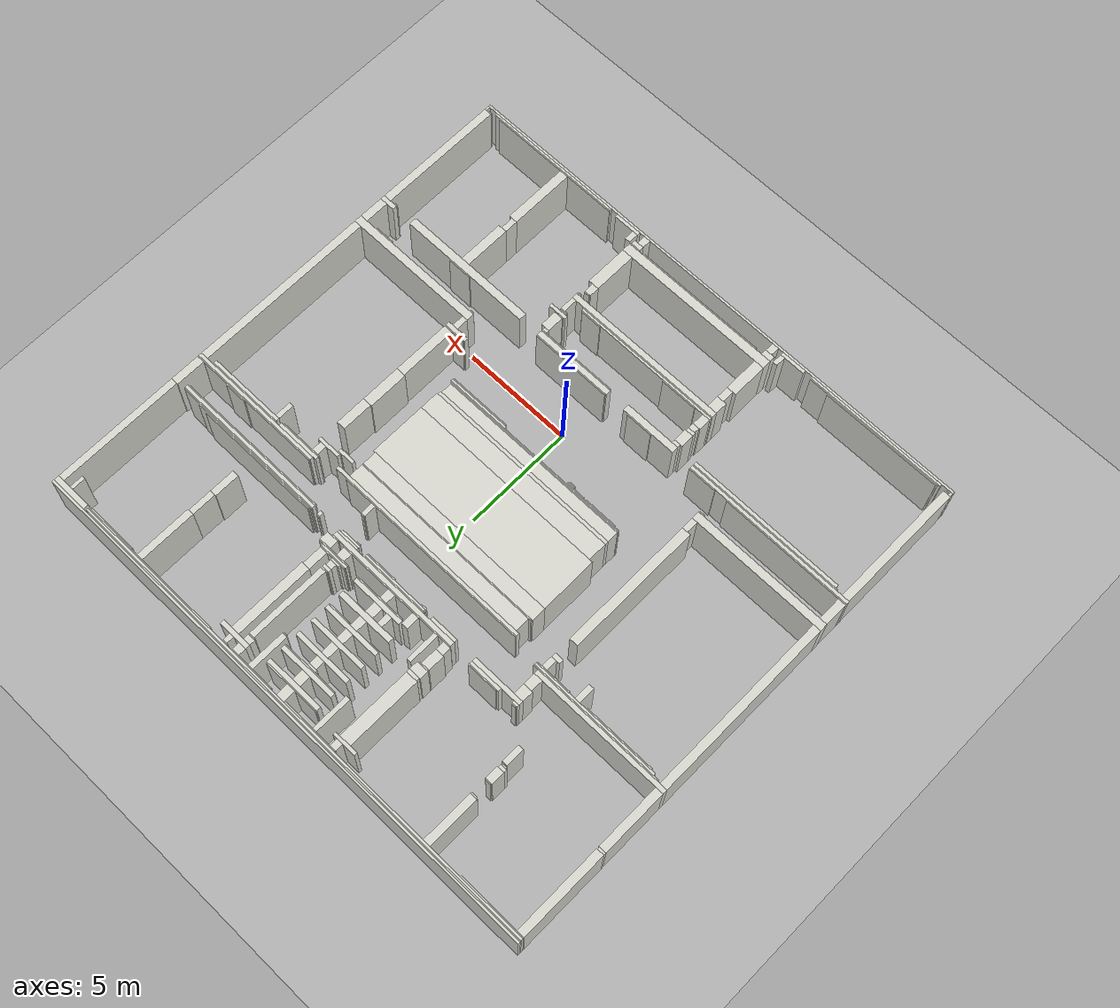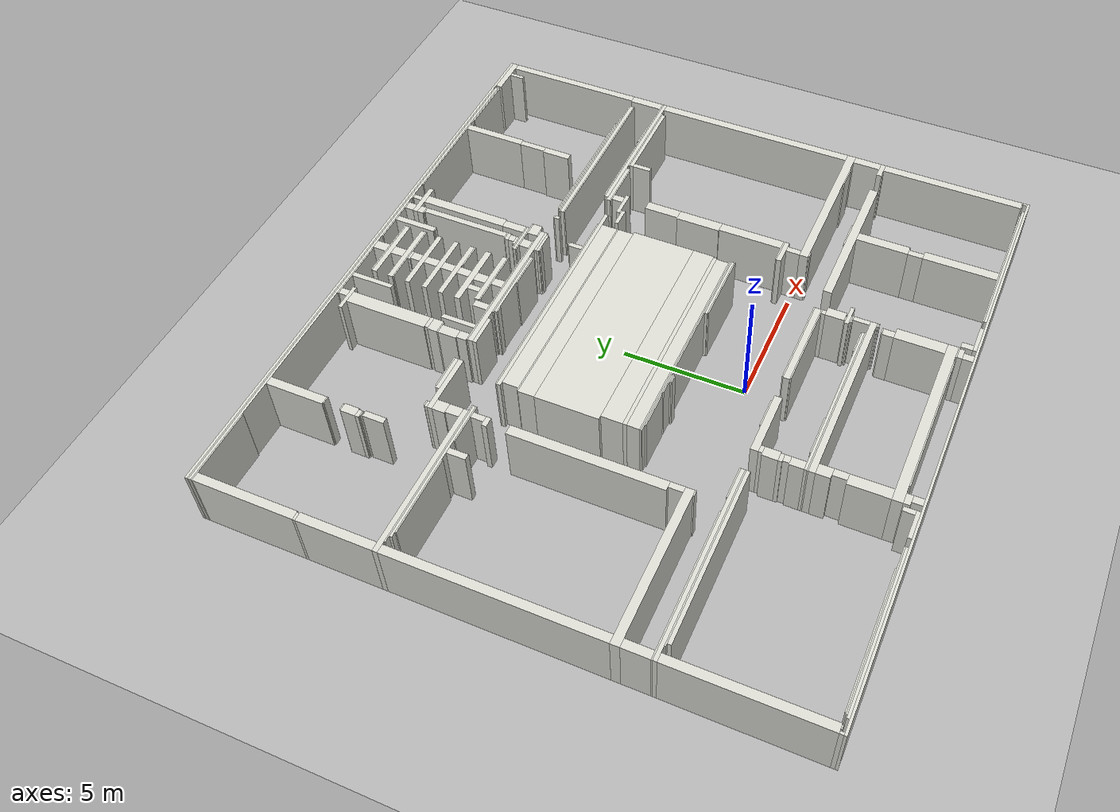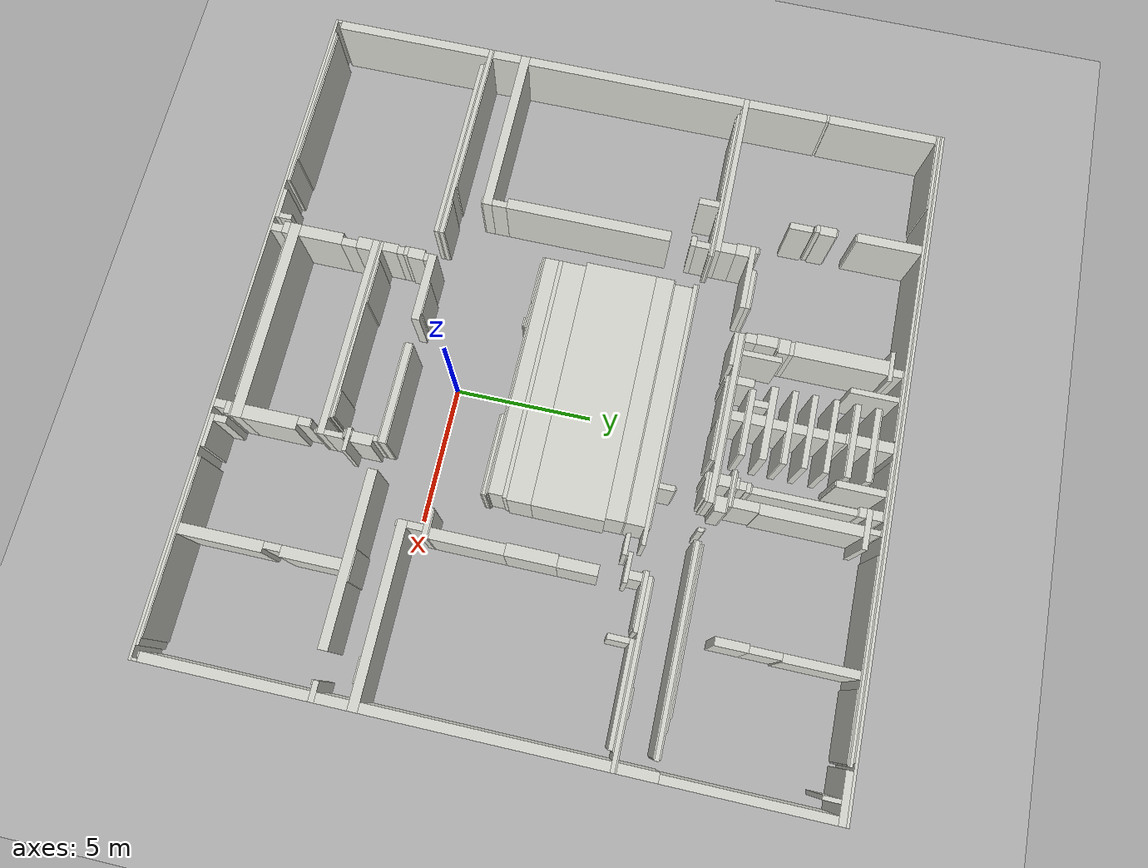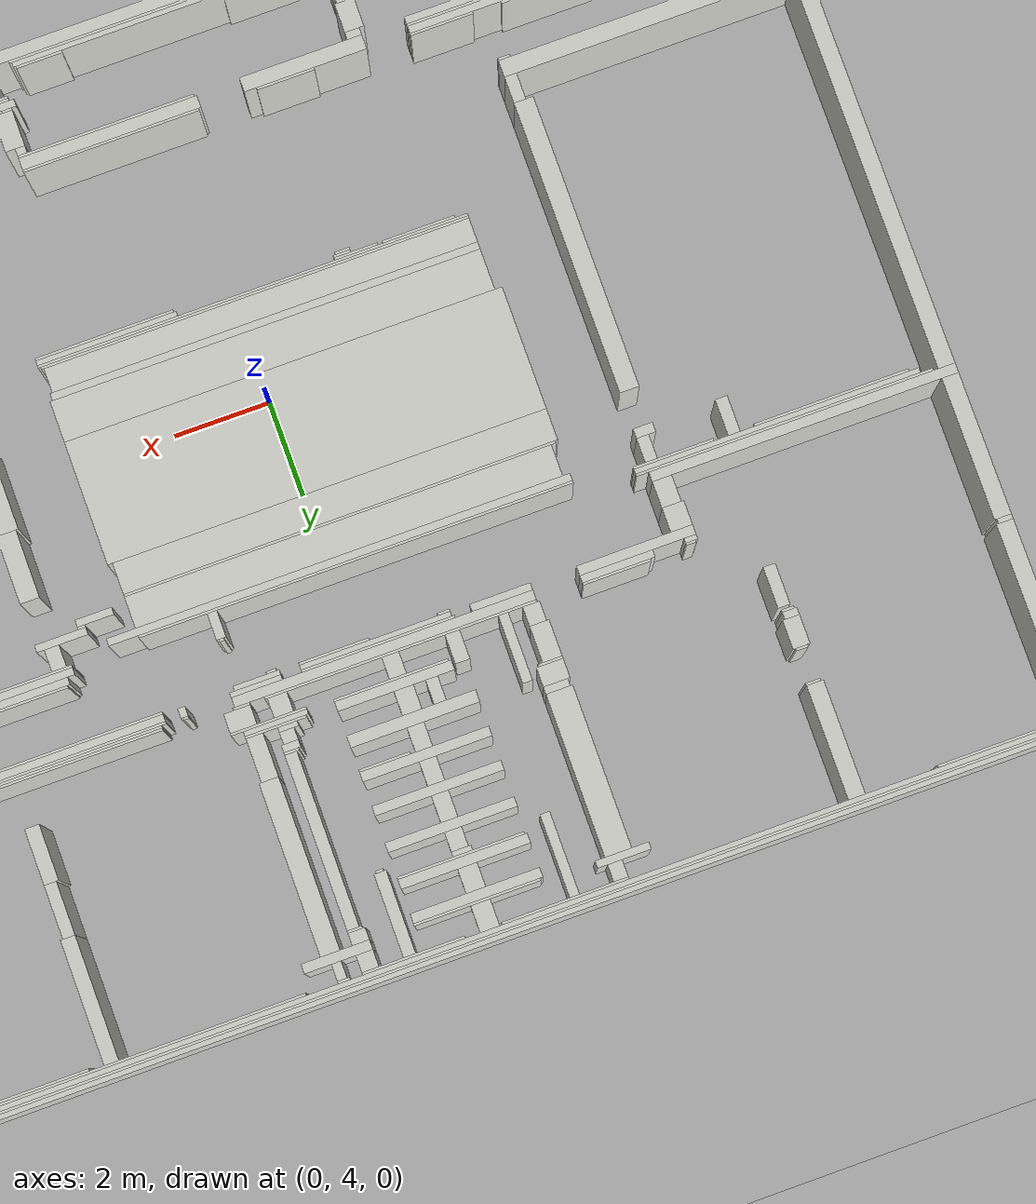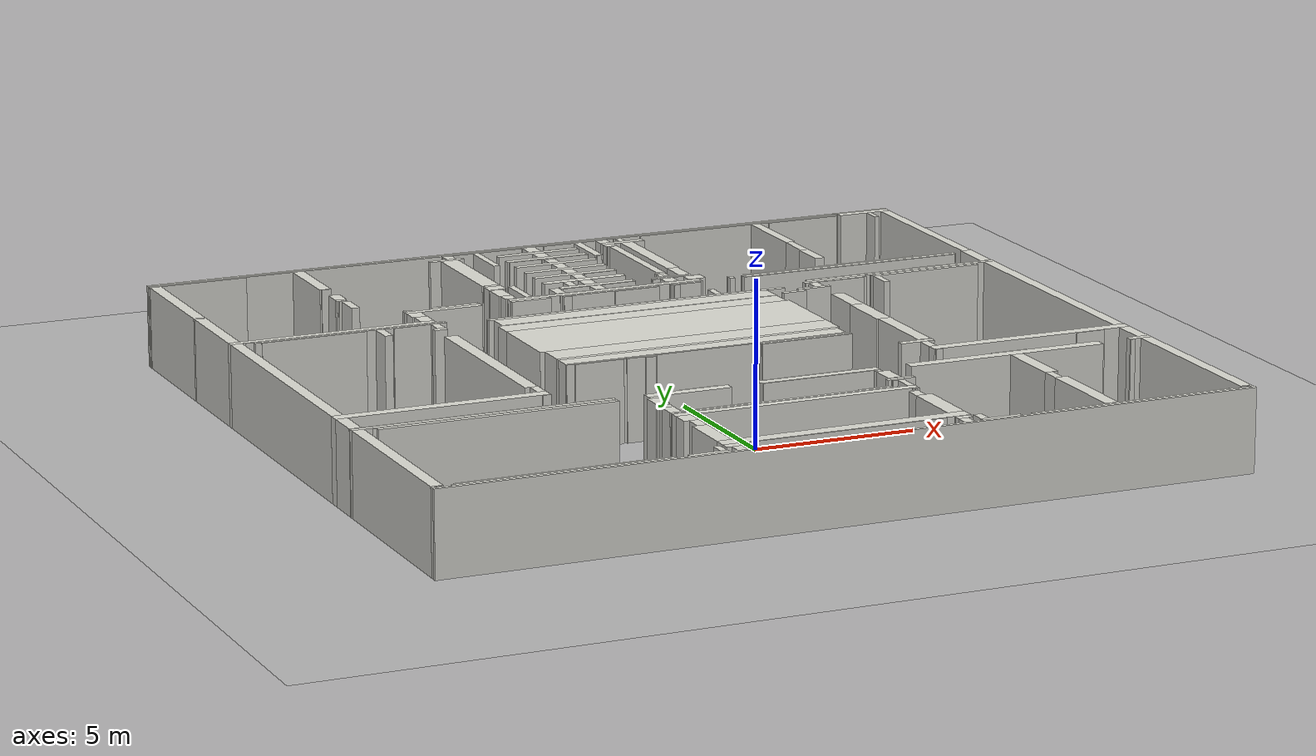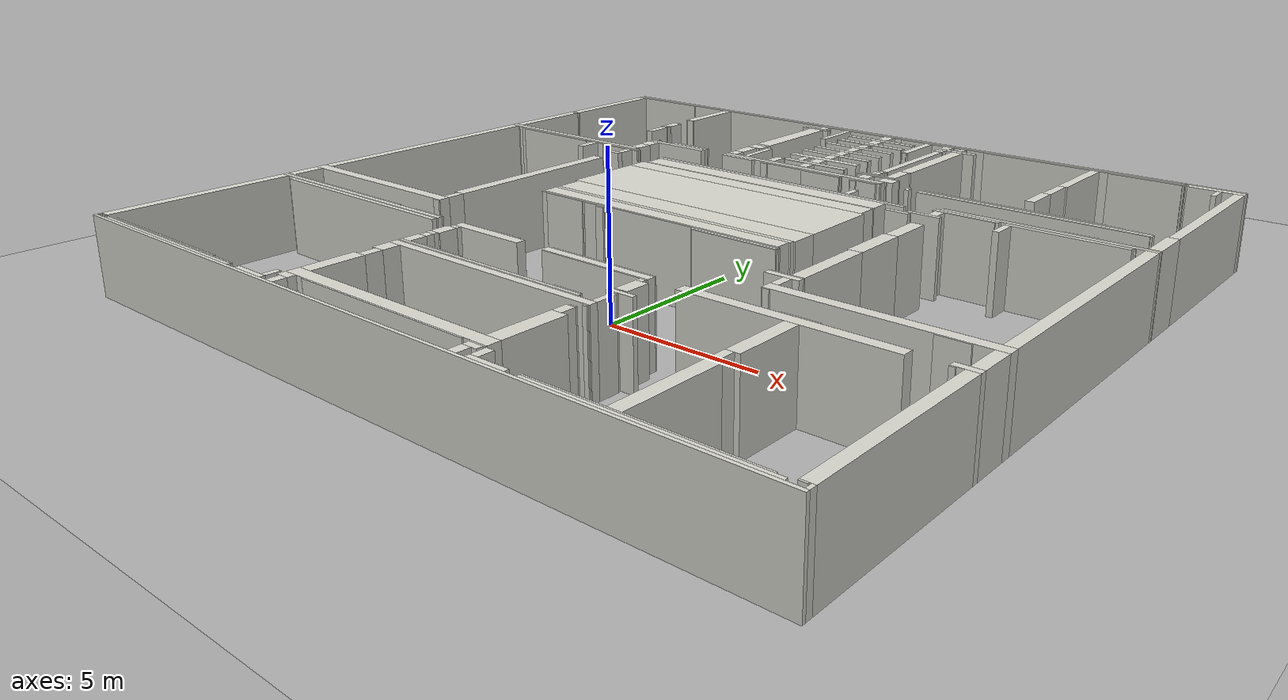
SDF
<sdf version="1.9">
 <world name="aischool_2f">
  <physics name="1ms" type="ignored">
   <max_step_size>0.001</max_step_size>
   <real_time_factor>1.0</real_time_factor>
  </physics>
  <plugin filename="gz-sim-physics-system" name="gz::sim::systems::Physics"/>
  <plugin filename="gz-sim-user-commands-system" name="gz::sim::systems::UserCommands"/>
  <plugin filename="gz-sim-scene-broadcaster-system" name="gz::sim::systems::SceneBroadcaster"/>
  <plugin filename="gz-sim-imu-system" name="gz::sim::systems::Imu"/>
  <plugin filename="gz-sim-sensors-system" name="gz::sim::systems::Sensors">
   <render_engine>ogre2</render_engine>
  </plugin>
  <light type="directional" name="sun">
   <pose>0 0 10 0 0 0</pose>
   <diffuse>0.8 0.8 0.8 1</diffuse>
   <specular>0.2 0.2 0.2 1</specular>
   <direction>-0.5 0.1 -0.9</direction>
  </light>
  <model name="ground_plane">
   <static>true</static>
   <link name="link">
    <collision name="collision">
     <geometry><plane><normal>0 0 1</normal><size>15 15</size></plane></geometry>
    </collision>
    <visual name="visual">
     <geometry><plane><normal>0 0 1</normal><size>15 15</size></plane></geometry>
     <material><ambient>0.7 0.7 0.7 1</ambient><diffuse>0.7 0.7 0.7 1</diffuse></material>
    </visual>
   </link>
  </model>
  <model name="aischool_2f_walls">
   <static>true</static>
   <link name="walls">
    <collision name="w0_c">
     <pose>-0.542 15.666 1.25 0 0 0</pose>
     <geometry><box><size>24.600 0.100 2.5</size></box></geometry>
    </collision>
    <visual name="w0_v">
     <pose>-0.542 15.666 1.25 0 0 0</pose>
     <geometry><box><size>24.600 0.100 2.5</size></box></geometry>
     <material><ambient>0.85 0.85 0.82 1</ambient><diffuse>0.85 0.85 0.82 1</diffuse></material>
    </visual>
    <collision name="w1_c">
     <pose>-1.517 15.591 1.25 0 0 0</pose>
     <geometry><box><size>22.650 0.050 2.5</size></box></geometry>
    </collision>
    <visual name="w1_v">
     <pose>-1.517 15.591 1.25 0 0 0</pose>
     <geometry><box><size>22.650 0.050 2.5</size></box></geometry>
     <material><ambient>0.85 0.85 0.82 1</ambient><diffuse>0.85 0.85 0.82 1</diffuse></material>
    </visual>
    <collision name="w2_c">
     <pose>-1.442 15.516 1.25 0 0 0</pose>
     <geometry><box><size>22.800 0.100 2.5</size></box></geometry>
    </collision>
    <visual name="w2_v">
     <pose>-1.442 15.516 1.25 0 0 0</pose>
     <geometry><box><size>22.800 0.100 2.5</size></box></geometry>
     <material><ambient>0.85 0.85 0.82 1</ambient><diffuse>0.85 0.85 0.82 1</diffuse></material>
    </visual>
    <collision name="w3_c">
     <pose>2.383 15.441 1.25 0 0 0</pose>
     <geometry><box><size>0.250 0.050 2.5</size></box></geometry>
    </collision>
    <visual name="w3_v">
     <pose>2.383 15.441 1.25 0 0 0</pose>
     <geometry><box><size>0.250 0.050 2.5</size></box></geometry>
     <material><ambient>0.85 0.85 0.82 1</ambient><diffuse>0.85 0.85 0.82 1</diffuse></material>
    </visual>
    <collision name="w4_c">
     <pose>-11.317 15.441 1.25 0 0 0</pose>
     <geometry><box><size>3.050 0.050 2.5</size></box></geometry>
    </collision>
    <visual name="w4_v">
     <pose>-11.317 15.441 1.25 0 0 0</pose>
     <geometry><box><size>3.050 0.050 2.5</size></box></geometry>
     <material><ambient>0.85 0.85 0.82 1</ambient><diffuse>0.85 0.85 0.82 1</diffuse></material>
    </visual>
    <collision name="w5_c">
     <pose>6.558 15.441 1.25 0 0 0</pose>
     <geometry><box><size>6.800 0.050 2.5</size></box></geometry>
    </collision>
    <visual name="w5_v">
     <pose>6.558 15.441 1.25 0 0 0</pose>
     <geometry><box><size>6.800 0.050 2.5</size></box></geometry>
     <material><ambient>0.85 0.85 0.82 1</ambient><diffuse>0.85 0.85 0.82 1</diffuse></material>
    </visual>
    <collision name="w6_c">
     <pose>0.958 15.441 1.25 0 0 0</pose>
     <geometry><box><size>2.100 0.050 2.5</size></box></geometry>
    </collision>
    <visual name="w6_v">
     <pose>0.958 15.441 1.25 0 0 0</pose>
     <geometry><box><size>2.100 0.050 2.5</size></box></geometry>
     <material><ambient>0.85 0.85 0.82 1</ambient><diffuse>0.85 0.85 0.82 1</diffuse></material>
    </visual>
    <collision name="w7_c">
     <pose>-2.142 15.441 1.25 0 0 0</pose>
     <geometry><box><size>2.600 0.050 2.5</size></box></geometry>
    </collision>
    <visual name="w7_v">
     <pose>-2.142 15.441 1.25 0 0 0</pose>
     <geometry><box><size>2.600 0.050 2.5</size></box></geometry>
     <material><ambient>0.85 0.85 0.82 1</ambient><diffuse>0.85 0.85 0.82 1</diffuse></material>
    </visual>
    <collision name="w8_c">
     <pose>10.908 15.491 1.25 0 0 0</pose>
     <geometry><box><size>1.700 0.250 2.5</size></box></geometry>
    </collision>
    <visual name="w8_v">
     <pose>10.908 15.491 1.25 0 0 0</pose>
     <geometry><box><size>1.700 0.250 2.5</size></box></geometry>
     <material><ambient>0.85 0.85 0.82 1</ambient><diffuse>0.85 0.85 0.82 1</diffuse></material>
    </visual>
    <collision name="w9_c">
     <pose>8.733 15.391 1.25 0 0 0</pose>
     <geometry><box><size>2.350 0.050 2.5</size></box></geometry>
    </collision>
    <visual name="w9_v">
     <pose>8.733 15.391 1.25 0 0 0</pose>
     <geometry><box><size>2.350 0.050 2.5</size></box></geometry>
     <material><ambient>0.85 0.85 0.82 1</ambient><diffuse>0.85 0.85 0.82 1</diffuse></material>
    </visual>
    <collision name="w10_c">
     <pose>-3.292 15.241 1.25 0 0 0</pose>
     <geometry><box><size>0.300 0.350 2.5</size></box></geometry>
    </collision>
    <visual name="w10_v">
     <pose>-3.292 15.241 1.25 0 0 0</pose>
     <geometry><box><size>0.300 0.350 2.5</size></box></geometry>
     <material><ambient>0.85 0.85 0.82 1</ambient><diffuse>0.85 0.85 0.82 1</diffuse></material>
    </visual>
    <collision name="w11_c">
     <pose>1.833 15.241 1.25 0 0 0</pose>
     <geometry><box><size>0.350 0.350 2.5</size></box></geometry>
    </collision>
    <visual name="w11_v">
     <pose>1.833 15.241 1.25 0 0 0</pose>
     <geometry><box><size>0.350 0.350 2.5</size></box></geometry>
     <material><ambient>0.85 0.85 0.82 1</ambient><diffuse>0.85 0.85 0.82 1</diffuse></material>
    </visual>
    <collision name="w12_c">
     <pose>2.408 15.241 1.25 0 0 0</pose>
     <geometry><box><size>0.200 0.350 2.5</size></box></geometry>
    </collision>
    <visual name="w12_v">
     <pose>2.408 15.241 1.25 0 0 0</pose>
     <geometry><box><size>0.200 0.350 2.5</size></box></geometry>
     <material><ambient>0.85 0.85 0.82 1</ambient><diffuse>0.85 0.85 0.82 1</diffuse></material>
    </visual>
    <collision name="w13_c">
     <pose>-0.592 15.191 1.25 0 0 0</pose>
     <geometry><box><size>0.400 0.550 2.5</size></box></geometry>
    </collision>
    <visual name="w13_v">
     <pose>-0.592 15.191 1.25 0 0 0</pose>
     <geometry><box><size>0.400 0.550 2.5</size></box></geometry>
     <material><ambient>0.85 0.85 0.82 1</ambient><diffuse>0.85 0.85 0.82 1</diffuse></material>
    </visual>
    <collision name="w14_c">
     <pose>-3.492 14.991 1.25 0 0 0</pose>
     <geometry><box><size>1.100 0.150 2.5</size></box></geometry>
    </collision>
    <visual name="w14_v">
     <pose>-3.492 14.991 1.25 0 0 0</pose>
     <geometry><box><size>1.100 0.150 2.5</size></box></geometry>
     <material><ambient>0.85 0.85 0.82 1</ambient><diffuse>0.85 0.85 0.82 1</diffuse></material>
    </visual>
    <collision name="w15_c">
     <pose>2.358 14.966 1.25 0 0 0</pose>
     <geometry><box><size>1.400 0.200 2.5</size></box></geometry>
    </collision>
    <visual name="w15_v">
     <pose>2.358 14.966 1.25 0 0 0</pose>
     <geometry><box><size>1.400 0.200 2.5</size></box></geometry>
     <material><ambient>0.85 0.85 0.82 1</ambient><diffuse>0.85 0.85 0.82 1</diffuse></material>
    </visual>
    <collision name="w16_c">
     <pose>-0.542 14.891 1.25 0 0 0</pose>
     <geometry><box><size>2.600 0.050 2.5</size></box></geometry>
    </collision>
    <visual name="w16_v">
     <pose>-0.542 14.891 1.25 0 0 0</pose>
     <geometry><box><size>2.600 0.050 2.5</size></box></geometry>
     <material><ambient>0.85 0.85 0.82 1</ambient><diffuse>0.85 0.85 0.82 1</diffuse></material>
    </visual>
    <collision name="w17_c">
     <pose>11.033 15.066 1.25 0 0 0</pose>
     <geometry><box><size>0.150 0.600 2.5</size></box></geometry>
    </collision>
    <visual name="w17_v">
     <pose>11.033 15.066 1.25 0 0 0</pose>
     <geometry><box><size>0.150 0.600 2.5</size></box></geometry>
     <material><ambient>0.85 0.85 0.82 1</ambient><diffuse>0.85 0.85 0.82 1</diffuse></material>
    </visual>
    <collision name="w18_c">
     <pose>-0.567 14.766 1.25 0 0 0</pose>
     <geometry><box><size>2.650 0.200 2.5</size></box></geometry>
    </collision>
    <visual name="w18_v">
     <pose>-0.567 14.766 1.25 0 0 0</pose>
     <geometry><box><size>2.650 0.200 2.5</size></box></geometry>
     <material><ambient>0.85 0.85 0.82 1</ambient><diffuse>0.85 0.85 0.82 1</diffuse></material>
    </visual>
    <collision name="w19_c">
     <pose>1.833 14.741 1.25 0 0 0</pose>
     <geometry><box><size>0.350 0.250 2.5</size></box></geometry>
    </collision>
    <visual name="w19_v">
     <pose>1.833 14.741 1.25 0 0 0</pose>
     <geometry><box><size>0.350 0.250 2.5</size></box></geometry>
     <material><ambient>0.85 0.85 0.82 1</ambient><diffuse>0.85 0.85 0.82 1</diffuse></material>
    </visual>
    <collision name="w20_c">
     <pose>1.858 14.591 1.25 0 0 0</pose>
     <geometry><box><size>0.300 0.050 2.5</size></box></geometry>
    </collision>
    <visual name="w20_v">
     <pose>1.858 14.591 1.25 0 0 0</pose>
     <geometry><box><size>0.300 0.050 2.5</size></box></geometry>
     <material><ambient>0.85 0.85 0.82 1</ambient><diffuse>0.85 0.85 0.82 1</diffuse></material>
    </visual>
    <collision name="w21_c">
     <pose>-0.592 14.416 1.25 0 0 0</pose>
     <geometry><box><size>0.400 0.500 2.5</size></box></geometry>
    </collision>
    <visual name="w21_v">
     <pose>-0.592 14.416 1.25 0 0 0</pose>
     <geometry><box><size>0.400 0.500 2.5</size></box></geometry>
     <material><ambient>0.85 0.85 0.82 1</ambient><diffuse>0.85 0.85 0.82 1</diffuse></material>
    </visual>
    <collision name="w22_c">
     <pose>-0.567 14.066 1.25 0 0 0</pose>
     <geometry><box><size>2.650 0.200 2.5</size></box></geometry>
    </collision>
    <visual name="w22_v">
     <pose>-0.567 14.066 1.25 0 0 0</pose>
     <geometry><box><size>2.650 0.200 2.5</size></box></geometry>
     <material><ambient>0.85 0.85 0.82 1</ambient><diffuse>0.85 0.85 0.82 1</diffuse></material>
    </visual>
    <collision name="w23_c">
     <pose>-0.542 13.941 1.25 0 0 0</pose>
     <geometry><box><size>2.600 0.050 2.5</size></box></geometry>
    </collision>
    <visual name="w23_v">
     <pose>-0.542 13.941 1.25 0 0 0</pose>
     <geometry><box><size>2.600 0.050 2.5</size></box></geometry>
     <material><ambient>0.85 0.85 0.82 1</ambient><diffuse>0.85 0.85 0.82 1</diffuse></material>
    </visual>
    <collision name="w24_c">
     <pose>-0.592 13.866 1.25 0 0 0</pose>
     <geometry><box><size>0.400 0.100 2.5</size></box></geometry>
    </collision>
    <visual name="w24_v">
     <pose>-0.592 13.866 1.25 0 0 0</pose>
     <geometry><box><size>0.400 0.100 2.5</size></box></geometry>
     <material><ambient>0.85 0.85 0.82 1</ambient><diffuse>0.85 0.85 0.82 1</diffuse></material>
    </visual>
    <collision name="w25_c">
     <pose>1.033 14.566 1.25 0 0 0</pose>
     <geometry><box><size>0.250 1.700 2.5</size></box></geometry>
    </collision>
    <visual name="w25_v">
     <pose>1.033 14.566 1.25 0 0 0</pose>
     <geometry><box><size>0.250 1.700 2.5</size></box></geometry>
     <material><ambient>0.85 0.85 0.82 1</ambient><diffuse>0.85 0.85 0.82 1</diffuse></material>
    </visual>
    <collision name="w26_c">
     <pose>-2.342 14.566 1.25 0 0 0</pose>
     <geometry><box><size>0.200 1.700 2.5</size></box></geometry>
    </collision>
    <visual name="w26_v">
     <pose>-2.342 14.566 1.25 0 0 0</pose>
     <geometry><box><size>0.200 1.700 2.5</size></box></geometry>
     <material><ambient>0.85 0.85 0.82 1</ambient><diffuse>0.85 0.85 0.82 1</diffuse></material>
    </visual>
    <collision name="w27_c">
     <pose>1.033 13.691 1.25 0 0 0</pose>
     <geometry><box><size>0.150 0.050 2.5</size></box></geometry>
    </collision>
    <visual name="w27_v">
     <pose>1.033 13.691 1.25 0 0 0</pose>
     <geometry><box><size>0.150 0.050 2.5</size></box></geometry>
     <material><ambient>0.85 0.85 0.82 1</ambient><diffuse>0.85 0.85 0.82 1</diffuse></material>
    </visual>
    <collision name="w28_c">
     <pose>-0.567 13.616 1.25 0 0 0</pose>
     <geometry><box><size>0.350 0.400 2.5</size></box></geometry>
    </collision>
    <visual name="w28_v">
     <pose>-0.567 13.616 1.25 0 0 0</pose>
     <geometry><box><size>0.350 0.400 2.5</size></box></geometry>
     <material><ambient>0.85 0.85 0.82 1</ambient><diffuse>0.85 0.85 0.82 1</diffuse></material>
    </visual>
    <collision name="w29_c">
     <pose>-0.567 13.316 1.25 0 0 0</pose>
     <geometry><box><size>2.650 0.200 2.5</size></box></geometry>
    </collision>
    <visual name="w29_v">
     <pose>-0.567 13.316 1.25 0 0 0</pose>
     <geometry><box><size>2.650 0.200 2.5</size></box></geometry>
     <material><ambient>0.85 0.85 0.82 1</ambient><diffuse>0.85 0.85 0.82 1</diffuse></material>
    </visual>
    <collision name="w30_c">
     <pose>-8.117 14.291 1.25 0 0 0</pose>
     <geometry><box><size>0.350 2.350 2.5</size></box></geometry>
    </collision>
    <visual name="w30_v">
     <pose>-8.117 14.291 1.25 0 0 0</pose>
     <geometry><box><size>0.350 2.350 2.5</size></box></geometry>
     <material><ambient>0.85 0.85 0.82 1</ambient><diffuse>0.85 0.85 0.82 1</diffuse></material>
    </visual>
    <collision name="w31_c">
     <pose>-8.092 13.091 1.25 0 0 0</pose>
     <geometry><box><size>0.300 0.050 2.5</size></box></geometry>
    </collision>
    <visual name="w31_v">
     <pose>-8.092 13.091 1.25 0 0 0</pose>
     <geometry><box><size>0.300 0.050 2.5</size></box></geometry>
     <material><ambient>0.85 0.85 0.82 1</ambient><diffuse>0.85 0.85 0.82 1</diffuse></material>
    </visual>
    <collision name="w32_c">
     <pose>7.108 14.141 1.25 0 0 0</pose>
     <geometry><box><size>0.300 2.550 2.5</size></box></geometry>
    </collision>
    <visual name="w32_v">
     <pose>7.108 14.141 1.25 0 0 0</pose>
     <geometry><box><size>0.300 2.550 2.5</size></box></geometry>
     <material><ambient>0.85 0.85 0.82 1</ambient><diffuse>0.85 0.85 0.82 1</diffuse></material>
    </visual>
    <collision name="w33_c">
     <pose>-0.567 12.941 1.25 0 0 0</pose>
     <geometry><box><size>0.350 0.550 2.5</size></box></geometry>
    </collision>
    <visual name="w33_v">
     <pose>-0.567 12.941 1.25 0 0 0</pose>
     <geometry><box><size>0.350 0.550 2.5</size></box></geometry>
     <material><ambient>0.85 0.85 0.82 1</ambient><diffuse>0.85 0.85 0.82 1</diffuse></material>
    </visual>
    <collision name="w34_c">
     <pose>-0.567 12.566 1.25 0 0 0</pose>
     <geometry><box><size>2.650 0.200 2.5</size></box></geometry>
    </collision>
    <visual name="w34_v">
     <pose>-0.567 12.566 1.25 0 0 0</pose>
     <geometry><box><size>2.650 0.200 2.5</size></box></geometry>
     <material><ambient>0.85 0.85 0.82 1</ambient><diffuse>0.85 0.85 0.82 1</diffuse></material>
    </visual>
    <collision name="w35_c">
     <pose>-8.117 12.391 1.25 0 0 0</pose>
     <geometry><box><size>0.250 0.050 2.5</size></box></geometry>
    </collision>
    <visual name="w35_v">
     <pose>-8.117 12.391 1.25 0 0 0</pose>
     <geometry><box><size>0.250 0.050 2.5</size></box></geometry>
     <material><ambient>0.85 0.85 0.82 1</ambient><diffuse>0.85 0.85 0.82 1</diffuse></material>
    </visual>
    <collision name="w36_c">
     <pose>-0.567 12.216 1.25 0 0 0</pose>
     <geometry><box><size>0.350 0.500 2.5</size></box></geometry>
    </collision>
    <visual name="w36_v">
     <pose>-0.567 12.216 1.25 0 0 0</pose>
     <geometry><box><size>0.350 0.500 2.5</size></box></geometry>
     <material><ambient>0.85 0.85 0.82 1</ambient><diffuse>0.85 0.85 0.82 1</diffuse></material>
    </visual>
    <collision name="w37_c">
     <pose>7.083 12.316 1.25 0 0 0</pose>
     <geometry><box><size>0.250 1.100 2.5</size></box></geometry>
    </collision>
    <visual name="w37_v">
     <pose>7.083 12.316 1.25 0 0 0</pose>
     <geometry><box><size>0.250 1.100 2.5</size></box></geometry>
     <material><ambient>0.85 0.85 0.82 1</ambient><diffuse>0.85 0.85 0.82 1</diffuse></material>
    </visual>
    <collision name="w38_c">
     <pose>-8.117 12.066 1.25 0 0 0</pose>
     <geometry><box><size>0.350 0.600 2.5</size></box></geometry>
    </collision>
    <visual name="w38_v">
     <pose>-8.117 12.066 1.25 0 0 0</pose>
     <geometry><box><size>0.350 0.600 2.5</size></box></geometry>
     <material><ambient>0.85 0.85 0.82 1</ambient><diffuse>0.85 0.85 0.82 1</diffuse></material>
    </visual>
    <collision name="w39_c">
     <pose>-0.567 11.866 1.25 0 0 0</pose>
     <geometry><box><size>2.650 0.200 2.5</size></box></geometry>
    </collision>
    <visual name="w39_v">
     <pose>-0.567 11.866 1.25 0 0 0</pose>
     <geometry><box><size>2.650 0.200 2.5</size></box></geometry>
     <material><ambient>0.85 0.85 0.82 1</ambient><diffuse>0.85 0.85 0.82 1</diffuse></material>
    </visual>
    <collision name="w40_c">
     <pose>0.233 11.741 1.25 0 0 0</pose>
     <geometry><box><size>1.050 0.050 2.5</size></box></geometry>
    </collision>
    <visual name="w40_v">
     <pose>0.233 11.741 1.25 0 0 0</pose>
     <geometry><box><size>1.050 0.050 2.5</size></box></geometry>
     <material><ambient>0.85 0.85 0.82 1</ambient><diffuse>0.85 0.85 0.82 1</diffuse></material>
    </visual>
    <collision name="w41_c">
     <pose>-8.142 11.691 1.25 0 0 0</pose>
     <geometry><box><size>0.300 0.150 2.5</size></box></geometry>
    </collision>
    <visual name="w41_v">
     <pose>-8.142 11.691 1.25 0 0 0</pose>
     <geometry><box><size>0.300 0.150 2.5</size></box></geometry>
     <material><ambient>0.85 0.85 0.82 1</ambient><diffuse>0.85 0.85 0.82 1</diffuse></material>
    </visual>
    <collision name="w42_c">
     <pose>-3.417 13.241 1.25 0 0 0</pose>
     <geometry><box><size>0.550 3.350 2.5</size></box></geometry>
    </collision>
    <visual name="w42_v">
     <pose>-3.417 13.241 1.25 0 0 0</pose>
     <geometry><box><size>0.550 3.350 2.5</size></box></geometry>
     <material><ambient>0.85 0.85 0.82 1</ambient><diffuse>0.85 0.85 0.82 1</diffuse></material>
    </visual>
    <collision name="w43_c">
     <pose>-8.117 11.591 1.25 0 0 0</pose>
     <geometry><box><size>0.250 0.050 2.5</size></box></geometry>
    </collision>
    <visual name="w43_v">
     <pose>-8.117 11.591 1.25 0 0 0</pose>
     <geometry><box><size>0.250 0.050 2.5</size></box></geometry>
     <material><ambient>0.85 0.85 0.82 1</ambient><diffuse>0.85 0.85 0.82 1</diffuse></material>
    </visual>
    <collision name="w44_c">
     <pose>-12.667 13.416 1.25 0 0 0</pose>
     <geometry><box><size>0.350 4.000 2.5</size></box></geometry>
    </collision>
    <visual name="w44_v">
     <pose>-12.667 13.416 1.25 0 0 0</pose>
     <geometry><box><size>0.350 4.000 2.5</size></box></geometry>
     <material><ambient>0.85 0.85 0.82 1</ambient><diffuse>0.85 0.85 0.82 1</diffuse></material>
    </visual>
    <collision name="w45_c">
     <pose>-3.392 11.491 1.25 0 0 0</pose>
     <geometry><box><size>0.500 0.150 2.5</size></box></geometry>
    </collision>
    <visual name="w45_v">
     <pose>-3.392 11.491 1.25 0 0 0</pose>
     <geometry><box><size>0.500 0.150 2.5</size></box></geometry>
     <material><ambient>0.85 0.85 0.82 1</ambient><diffuse>0.85 0.85 0.82 1</diffuse></material>
    </visual>
    <collision name="w46_c">
     <pose>2.458 13.091 1.25 0 0 0</pose>
     <geometry><box><size>0.400 3.550 2.5</size></box></geometry>
    </collision>
    <visual name="w46_v">
     <pose>2.458 13.091 1.25 0 0 0</pose>
     <geometry><box><size>0.400 3.550 2.5</size></box></geometry>
     <material><ambient>0.85 0.85 0.82 1</ambient><diffuse>0.85 0.85 0.82 1</diffuse></material>
    </visual>
    <collision name="w47_c">
     <pose>-12.692 11.366 1.25 0 0 0</pose>
     <geometry><box><size>0.300 0.100 2.5</size></box></geometry>
    </collision>
    <visual name="w47_v">
     <pose>-12.692 11.366 1.25 0 0 0</pose>
     <geometry><box><size>0.300 0.100 2.5</size></box></geometry>
     <material><ambient>0.85 0.85 0.82 1</ambient><diffuse>0.85 0.85 0.82 1</diffuse></material>
    </visual>
    <collision name="w48_c">
     <pose>-0.567 11.516 1.25 0 0 0</pose>
     <geometry><box><size>0.350 0.500 2.5</size></box></geometry>
    </collision>
    <visual name="w48_v">
     <pose>-0.567 11.516 1.25 0 0 0</pose>
     <geometry><box><size>0.350 0.500 2.5</size></box></geometry>
     <material><ambient>0.85 0.85 0.82 1</ambient><diffuse>0.85 0.85 0.82 1</diffuse></material>
    </visual>
    <collision name="w49_c">
     <pose>-3.417 11.216 1.25 0 0 0</pose>
     <geometry><box><size>0.550 0.400 2.5</size></box></geometry>
    </collision>
    <visual name="w49_v">
     <pose>-3.417 11.216 1.25 0 0 0</pose>
     <geometry><box><size>0.550 0.400 2.5</size></box></geometry>
     <material><ambient>0.85 0.85 0.82 1</ambient><diffuse>0.85 0.85 0.82 1</diffuse></material>
    </visual>
    <collision name="w50_c">
     <pose>-0.567 11.141 1.25 0 0 0</pose>
     <geometry><box><size>2.650 0.250 2.5</size></box></geometry>
    </collision>
    <visual name="w50_v">
     <pose>-0.567 11.141 1.25 0 0 0</pose>
     <geometry><box><size>2.650 0.250 2.5</size></box></geometry>
     <material><ambient>0.85 0.85 0.82 1</ambient><diffuse>0.85 0.85 0.82 1</diffuse></material>
    </visual>
    <collision name="w51_c">
     <pose>1.883 12.766 1.25 0 0 0</pose>
     <geometry><box><size>0.250 3.600 2.5</size></box></geometry>
    </collision>
    <visual name="w51_v">
     <pose>1.883 12.766 1.25 0 0 0</pose>
     <geometry><box><size>0.250 3.600 2.5</size></box></geometry>
     <material><ambient>0.85 0.85 0.82 1</ambient><diffuse>0.85 0.85 0.82 1</diffuse></material>
    </visual>
    <collision name="w52_c">
     <pose>-3.442 10.991 1.25 0 0 0</pose>
     <geometry><box><size>0.500 0.050 2.5</size></box></geometry>
    </collision>
    <visual name="w52_v">
     <pose>-3.442 10.991 1.25 0 0 0</pose>
     <geometry><box><size>0.500 0.050 2.5</size></box></geometry>
     <material><ambient>0.85 0.85 0.82 1</ambient><diffuse>0.85 0.85 0.82 1</diffuse></material>
    </visual>
    <collision name="w53_c">
     <pose>1.858 10.941 1.25 0 0 0</pose>
     <geometry><box><size>0.300 0.050 2.5</size></box></geometry>
    </collision>
    <visual name="w53_v">
     <pose>1.858 10.941 1.25 0 0 0</pose>
     <geometry><box><size>0.300 0.050 2.5</size></box></geometry>
     <material><ambient>0.85 0.85 0.82 1</ambient><diffuse>0.85 0.85 0.82 1</diffuse></material>
    </visual>
    <collision name="w54_c">
     <pose>1.833 10.841 1.25 0 0 0</pose>
     <geometry><box><size>0.350 0.150 2.5</size></box></geometry>
    </collision>
    <visual name="w54_v">
     <pose>1.833 10.841 1.25 0 0 0</pose>
     <geometry><box><size>0.350 0.150 2.5</size></box></geometry>
     <material><ambient>0.85 0.85 0.82 1</ambient><diffuse>0.85 0.85 0.82 1</diffuse></material>
    </visual>
    <collision name="w55_c">
     <pose>-8.067 11.091 1.25 0 0 0</pose>
     <geometry><box><size>0.250 0.850 2.5</size></box></geometry>
    </collision>
    <visual name="w55_v">
     <pose>-8.067 11.091 1.25 0 0 0</pose>
     <geometry><box><size>0.250 0.850 2.5</size></box></geometry>
     <material><ambient>0.85 0.85 0.82 1</ambient><diffuse>0.85 0.85 0.82 1</diffuse></material>
    </visual>
    <collision name="w56_c">
     <pose>7.058 11.191 1.25 0 0 0</pose>
     <geometry><box><size>0.300 1.150 2.5</size></box></geometry>
    </collision>
    <visual name="w56_v">
     <pose>7.058 11.191 1.25 0 0 0</pose>
     <geometry><box><size>0.300 1.150 2.5</size></box></geometry>
     <material><ambient>0.85 0.85 0.82 1</ambient><diffuse>0.85 0.85 0.82 1</diffuse></material>
    </visual>
    <collision name="w57_c">
     <pose>-1.167 10.766 1.25 0 0 0</pose>
     <geometry><box><size>0.250 0.500 2.5</size></box></geometry>
    </collision>
    <visual name="w57_v">
     <pose>-1.167 10.766 1.25 0 0 0</pose>
     <geometry><box><size>0.250 0.500 2.5</size></box></geometry>
     <material><ambient>0.85 0.85 0.82 1</ambient><diffuse>0.85 0.85 0.82 1</diffuse></material>
    </visual>
    <collision name="w58_c">
     <pose>-0.592 10.766 1.25 0 0 0</pose>
     <geometry><box><size>0.400 0.500 2.5</size></box></geometry>
    </collision>
    <visual name="w58_v">
     <pose>-0.592 10.766 1.25 0 0 0</pose>
     <geometry><box><size>0.400 0.500 2.5</size></box></geometry>
     <material><ambient>0.85 0.85 0.82 1</ambient><diffuse>0.85 0.85 0.82 1</diffuse></material>
    </visual>
    <collision name="w59_c">
     <pose>1.808 10.641 1.25 0 0 0</pose>
     <geometry><box><size>0.300 0.250 2.5</size></box></geometry>
    </collision>
    <visual name="w59_v">
     <pose>1.808 10.641 1.25 0 0 0</pose>
     <geometry><box><size>0.300 0.250 2.5</size></box></geometry>
     <material><ambient>0.85 0.85 0.82 1</ambient><diffuse>0.85 0.85 0.82 1</diffuse></material>
    </visual>
    <collision name="w60_c">
     <pose>2.433 10.866 1.25 0 0 0</pose>
     <geometry><box><size>0.350 0.900 2.5</size></box></geometry>
    </collision>
    <visual name="w60_v">
     <pose>2.433 10.866 1.25 0 0 0</pose>
     <geometry><box><size>0.350 0.900 2.5</size></box></geometry>
     <material><ambient>0.85 0.85 0.82 1</ambient><diffuse>0.85 0.85 0.82 1</diffuse></material>
    </visual>
    <collision name="w61_c">
     <pose>1.758 10.466 1.25 0 0 0</pose>
     <geometry><box><size>0.400 0.100 2.5</size></box></geometry>
    </collision>
    <visual name="w61_v">
     <pose>1.758 10.466 1.25 0 0 0</pose>
     <geometry><box><size>0.400 0.100 2.5</size></box></geometry>
     <material><ambient>0.85 0.85 0.82 1</ambient><diffuse>0.85 0.85 0.82 1</diffuse></material>
    </visual>
    <collision name="w62_c">
     <pose>1.983 10.391 1.25 0 0 0</pose>
     <geometry><box><size>1.250 0.050 2.5</size></box></geometry>
    </collision>
    <visual name="w62_v">
     <pose>1.983 10.391 1.25 0 0 0</pose>
     <geometry><box><size>1.250 0.050 2.5</size></box></geometry>
     <material><ambient>0.85 0.85 0.82 1</ambient><diffuse>0.85 0.85 0.82 1</diffuse></material>
    </visual>
    <collision name="w63_c">
     <pose>-0.442 10.416 1.25 0 0 0</pose>
     <geometry><box><size>2.400 0.200 2.5</size></box></geometry>
    </collision>
    <visual name="w63_v">
     <pose>-0.442 10.416 1.25 0 0 0</pose>
     <geometry><box><size>2.400 0.200 2.5</size></box></geometry>
     <material><ambient>0.85 0.85 0.82 1</ambient><diffuse>0.85 0.85 0.82 1</diffuse></material>
    </visual>
    <collision name="w64_c">
     <pose>1.958 10.316 1.25 0 0 0</pose>
     <geometry><box><size>1.300 0.100 2.5</size></box></geometry>
    </collision>
    <visual name="w64_v">
     <pose>1.958 10.316 1.25 0 0 0</pose>
     <geometry><box><size>1.300 0.100 2.5</size></box></geometry>
     <material><ambient>0.85 0.85 0.82 1</ambient><diffuse>0.85 0.85 0.82 1</diffuse></material>
    </visual>
    <collision name="w65_c">
     <pose>-0.417 10.291 1.25 0 0 0</pose>
     <geometry><box><size>2.350 0.050 2.5</size></box></geometry>
    </collision>
    <visual name="w65_v">
     <pose>-0.417 10.291 1.25 0 0 0</pose>
     <geometry><box><size>2.350 0.050 2.5</size></box></geometry>
     <material><ambient>0.85 0.85 0.82 1</ambient><diffuse>0.85 0.85 0.82 1</diffuse></material>
    </visual>
    <collision name="w66_c">
     <pose>-3.492 10.591 1.25 0 0 0</pose>
     <geometry><box><size>0.400 0.750 2.5</size></box></geometry>
    </collision>
    <visual name="w66_v">
     <pose>-3.492 10.591 1.25 0 0 0</pose>
     <geometry><box><size>0.400 0.750 2.5</size></box></geometry>
     <material><ambient>0.85 0.85 0.82 1</ambient><diffuse>0.85 0.85 0.82 1</diffuse></material>
    </visual>
    <collision name="w67_c">
     <pose>2.083 10.241 1.25 0 0 0</pose>
     <geometry><box><size>1.550 0.050 2.5</size></box></geometry>
    </collision>
    <visual name="w67_v">
     <pose>2.083 10.241 1.25 0 0 0</pose>
     <geometry><box><size>1.550 0.050 2.5</size></box></geometry>
     <material><ambient>0.85 0.85 0.82 1</ambient><diffuse>0.85 0.85 0.82 1</diffuse></material>
    </visual>
    <collision name="w68_c">
     <pose>-2.892 10.516 1.25 0 0 0</pose>
     <geometry><box><size>0.200 1.400 2.5</size></box></geometry>
    </collision>
    <visual name="w68_v">
     <pose>-2.892 10.516 1.25 0 0 0</pose>
     <geometry><box><size>0.200 1.400 2.5</size></box></geometry>
     <material><ambient>0.85 0.85 0.82 1</ambient><diffuse>0.85 0.85 0.82 1</diffuse></material>
    </visual>
    <collision name="w69_c">
     <pose>-1.842 10.116 1.25 0 0 0</pose>
     <geometry><box><size>0.300 0.600 2.5</size></box></geometry>
    </collision>
    <visual name="w69_v">
     <pose>-1.842 10.116 1.25 0 0 0</pose>
     <geometry><box><size>0.300 0.600 2.5</size></box></geometry>
     <material><ambient>0.85 0.85 0.82 1</ambient><diffuse>0.85 0.85 0.82 1</diffuse></material>
    </visual>
    <collision name="w70_c">
     <pose>-0.567 10.041 1.25 0 0 0</pose>
     <geometry><box><size>0.350 0.450 2.5</size></box></geometry>
    </collision>
    <visual name="w70_v">
     <pose>-0.567 10.041 1.25 0 0 0</pose>
     <geometry><box><size>0.350 0.450 2.5</size></box></geometry>
     <material><ambient>0.85 0.85 0.82 1</ambient><diffuse>0.85 0.85 0.82 1</diffuse></material>
    </visual>
    <collision name="w71_c">
     <pose>2.583 10.016 1.25 0 0 0</pose>
     <geometry><box><size>0.550 0.400 2.5</size></box></geometry>
    </collision>
    <visual name="w71_v">
     <pose>2.583 10.016 1.25 0 0 0</pose>
     <geometry><box><size>0.550 0.400 2.5</size></box></geometry>
     <material><ambient>0.85 0.85 0.82 1</ambient><diffuse>0.85 0.85 0.82 1</diffuse></material>
    </visual>
    <collision name="w72_c">
     <pose>-3.467 10.016 1.25 0 0 0</pose>
     <geometry><box><size>0.350 0.400 2.5</size></box></geometry>
    </collision>
    <visual name="w72_v">
     <pose>-3.467 10.016 1.25 0 0 0</pose>
     <geometry><box><size>0.350 0.400 2.5</size></box></geometry>
     <material><ambient>0.85 0.85 0.82 1</ambient><diffuse>0.85 0.85 0.82 1</diffuse></material>
    </visual>
    <collision name="w73_c">
     <pose>1.758 10.016 1.25 0 0 0</pose>
     <geometry><box><size>0.400 0.400 2.5</size></box></geometry>
    </collision>
    <visual name="w73_v">
     <pose>1.758 10.016 1.25 0 0 0</pose>
     <geometry><box><size>0.400 0.400 2.5</size></box></geometry>
     <material><ambient>0.85 0.85 0.82 1</ambient><diffuse>0.85 0.85 0.82 1</diffuse></material>
    </visual>
    <collision name="w74_c">
     <pose>-0.792 9.791 1.25 0 0 0</pose>
     <geometry><box><size>5.600 0.050 2.5</size></box></geometry>
    </collision>
    <visual name="w74_v">
     <pose>-0.792 9.791 1.25 0 0 0</pose>
     <geometry><box><size>5.600 0.050 2.5</size></box></geometry>
     <material><ambient>0.85 0.85 0.82 1</ambient><diffuse>0.85 0.85 0.82 1</diffuse></material>
    </visual>
    <collision name="w75_c">
     <pose>-5.242 9.791 1.25 0 0 0</pose>
     <geometry><box><size>1.400 0.050 2.5</size></box></geometry>
    </collision>
    <visual name="w75_v">
     <pose>-5.242 9.791 1.25 0 0 0</pose>
     <geometry><box><size>1.400 0.050 2.5</size></box></geometry>
     <material><ambient>0.85 0.85 0.82 1</ambient><diffuse>0.85 0.85 0.82 1</diffuse></material>
    </visual>
    <collision name="w76_c">
     <pose>2.483 9.791 1.25 0 0 0</pose>
     <geometry><box><size>0.350 0.050 2.5</size></box></geometry>
    </collision>
    <visual name="w76_v">
     <pose>2.483 9.791 1.25 0 0 0</pose>
     <geometry><box><size>0.350 0.050 2.5</size></box></geometry>
     <material><ambient>0.85 0.85 0.82 1</ambient><diffuse>0.85 0.85 0.82 1</diffuse></material>
    </visual>
    <collision name="w77_c">
     <pose>-6.792 9.741 1.25 0 0 0</pose>
     <geometry><box><size>0.200 0.050 2.5</size></box></geometry>
    </collision>
    <visual name="w77_v">
     <pose>-6.792 9.741 1.25 0 0 0</pose>
     <geometry><box><size>0.200 0.050 2.5</size></box></geometry>
     <material><ambient>0.85 0.85 0.82 1</ambient><diffuse>0.85 0.85 0.82 1</diffuse></material>
    </visual>
    <collision name="w78_c">
     <pose>11.608 12.516 1.25 0 0 0</pose>
     <geometry><box><size>0.300 5.700 2.5</size></box></geometry>
    </collision>
    <visual name="w78_v">
     <pose>11.608 12.516 1.25 0 0 0</pose>
     <geometry><box><size>0.300 5.700 2.5</size></box></geometry>
     <material><ambient>0.85 0.85 0.82 1</ambient><diffuse>0.85 0.85 0.82 1</diffuse></material>
    </visual>
    <collision name="w79_c">
     <pose>6.908 9.691 1.25 0 0 0</pose>
     <geometry><box><size>5.700 0.050 2.5</size></box></geometry>
    </collision>
    <visual name="w79_v">
     <pose>6.908 9.691 1.25 0 0 0</pose>
     <geometry><box><size>5.700 0.050 2.5</size></box></geometry>
     <material><ambient>0.85 0.85 0.82 1</ambient><diffuse>0.85 0.85 0.82 1</diffuse></material>
    </visual>
    <collision name="w80_c">
     <pose>-5.292 9.691 1.25 0 0 0</pose>
     <geometry><box><size>1.500 0.150 2.5</size></box></geometry>
    </collision>
    <visual name="w80_v">
     <pose>-5.292 9.691 1.25 0 0 0</pose>
     <geometry><box><size>1.500 0.150 2.5</size></box></geometry>
     <material><ambient>0.85 0.85 0.82 1</ambient><diffuse>0.85 0.85 0.82 1</diffuse></material>
    </visual>
    <collision name="w81_c">
     <pose>-6.817 9.666 1.25 0 0 0</pose>
     <geometry><box><size>0.250 0.100 2.5</size></box></geometry>
    </collision>
    <visual name="w81_v">
     <pose>-6.817 9.666 1.25 0 0 0</pose>
     <geometry><box><size>0.250 0.100 2.5</size></box></geometry>
     <material><ambient>0.85 0.85 0.82 1</ambient><diffuse>0.85 0.85 0.82 1</diffuse></material>
    </visual>
    <collision name="w82_c">
     <pose>3.558 9.641 1.25 0 0 0</pose>
     <geometry><box><size>0.100 0.050 2.5</size></box></geometry>
    </collision>
    <visual name="w82_v">
     <pose>3.558 9.641 1.25 0 0 0</pose>
     <geometry><box><size>0.100 0.050 2.5</size></box></geometry>
     <material><ambient>0.85 0.85 0.82 1</ambient><diffuse>0.85 0.85 0.82 1</diffuse></material>
    </visual>
    <collision name="w83_c">
     <pose>7.133 9.641 1.25 0 0 0</pose>
     <geometry><box><size>6.150 0.050 2.5</size></box></geometry>
    </collision>
    <visual name="w83_v">
     <pose>7.133 9.641 1.25 0 0 0</pose>
     <geometry><box><size>6.150 0.050 2.5</size></box></geometry>
     <material><ambient>0.85 0.85 0.82 1</ambient><diffuse>0.85 0.85 0.82 1</diffuse></material>
    </visual>
    <collision name="w84_c">
     <pose>-0.492 9.666 1.25 0 0 0</pose>
     <geometry><box><size>6.200 0.200 2.5</size></box></geometry>
    </collision>
    <visual name="w84_v">
     <pose>-0.492 9.666 1.25 0 0 0</pose>
     <geometry><box><size>6.200 0.200 2.5</size></box></geometry>
     <material><ambient>0.85 0.85 0.82 1</ambient><diffuse>0.85 0.85 0.82 1</diffuse></material>
    </visual>
    <collision name="w85_c">
     <pose>7.508 9.591 1.25 0 0 0</pose>
     <geometry><box><size>7.100 0.050 2.5</size></box></geometry>
    </collision>
    <visual name="w85_v">
     <pose>7.508 9.591 1.25 0 0 0</pose>
     <geometry><box><size>7.100 0.050 2.5</size></box></geometry>
     <material><ambient>0.85 0.85 0.82 1</ambient><diffuse>0.85 0.85 0.82 1</diffuse></material>
    </visual>
    <collision name="w86_c">
     <pose>-0.417 9.541 1.25 0 0 0</pose>
     <geometry><box><size>3.150 0.050 2.5</size></box></geometry>
    </collision>
    <visual name="w86_v">
     <pose>-0.417 9.541 1.25 0 0 0</pose>
     <geometry><box><size>3.150 0.050 2.5</size></box></geometry>
     <material><ambient>0.85 0.85 0.82 1</ambient><diffuse>0.85 0.85 0.82 1</diffuse></material>
    </visual>
    <collision name="w87_c">
     <pose>2.083 9.516 1.25 0 0 0</pose>
     <geometry><box><size>1.050 0.100 2.5</size></box></geometry>
    </collision>
    <visual name="w87_v">
     <pose>2.083 9.516 1.25 0 0 0</pose>
     <geometry><box><size>1.050 0.100 2.5</size></box></geometry>
     <material><ambient>0.85 0.85 0.82 1</ambient><diffuse>0.85 0.85 0.82 1</diffuse></material>
    </visual>
    <collision name="w88_c">
     <pose>-5.742 9.516 1.25 0 0 0</pose>
     <geometry><box><size>2.400 0.200 2.5</size></box></geometry>
    </collision>
    <visual name="w88_v">
     <pose>-5.742 9.516 1.25 0 0 0</pose>
     <geometry><box><size>2.400 0.200 2.5</size></box></geometry>
     <material><ambient>0.85 0.85 0.82 1</ambient><diffuse>0.85 0.85 0.82 1</diffuse></material>
    </visual>
    <collision name="w89_c">
     <pose>3.583 9.516 1.25 0 0 0</pose>
     <geometry><box><size>0.150 0.200 2.5</size></box></geometry>
    </collision>
    <visual name="w89_v">
     <pose>3.583 9.516 1.25 0 0 0</pose>
     <geometry><box><size>0.150 0.200 2.5</size></box></geometry>
     <material><ambient>0.85 0.85 0.82 1</ambient><diffuse>0.85 0.85 0.82 1</diffuse></material>
    </visual>
    <collision name="w90_c">
     <pose>-2.967 9.491 1.25 0 0 0</pose>
     <geometry><box><size>1.250 0.150 2.5</size></box></geometry>
    </collision>
    <visual name="w90_v">
     <pose>-2.967 9.491 1.25 0 0 0</pose>
     <geometry><box><size>1.250 0.150 2.5</size></box></geometry>
     <material><ambient>0.85 0.85 0.82 1</ambient><diffuse>0.85 0.85 0.82 1</diffuse></material>
    </visual>
    <collision name="w91_c">
     <pose>7.533 9.491 1.25 0 0 0</pose>
     <geometry><box><size>7.150 0.150 2.5</size></box></geometry>
    </collision>
    <visual name="w91_v">
     <pose>7.533 9.491 1.25 0 0 0</pose>
     <geometry><box><size>7.150 0.150 2.5</size></box></geometry>
     <material><ambient>0.85 0.85 0.82 1</ambient><diffuse>0.85 0.85 0.82 1</diffuse></material>
    </visual>
    <collision name="w92_c">
     <pose>-0.392 9.466 1.25 0 0 0</pose>
     <geometry><box><size>3.100 0.100 2.5</size></box></geometry>
    </collision>
    <visual name="w92_v">
     <pose>-0.392 9.466 1.25 0 0 0</pose>
     <geometry><box><size>3.100 0.100 2.5</size></box></geometry>
     <material><ambient>0.85 0.85 0.82 1</ambient><diffuse>0.85 0.85 0.82 1</diffuse></material>
    </visual>
    <collision name="w93_c">
     <pose>2.033 9.416 1.25 0 0 0</pose>
     <geometry><box><size>0.950 0.100 2.5</size></box></geometry>
    </collision>
    <visual name="w93_v">
     <pose>2.033 9.416 1.25 0 0 0</pose>
     <geometry><box><size>0.950 0.100 2.5</size></box></geometry>
     <material><ambient>0.85 0.85 0.82 1</ambient><diffuse>0.85 0.85 0.82 1</diffuse></material>
    </visual>
    <collision name="w94_c">
     <pose>0.433 9.391 1.25 0 0 0</pose>
     <geometry><box><size>1.450 0.050 2.5</size></box></geometry>
    </collision>
    <visual name="w94_v">
     <pose>0.433 9.391 1.25 0 0 0</pose>
     <geometry><box><size>1.450 0.050 2.5</size></box></geometry>
     <material><ambient>0.85 0.85 0.82 1</ambient><diffuse>0.85 0.85 0.82 1</diffuse></material>
    </visual>
    <collision name="w95_c">
     <pose>-1.817 9.391 1.25 0 0 0</pose>
     <geometry><box><size>0.250 0.050 2.5</size></box></geometry>
    </collision>
    <visual name="w95_v">
     <pose>-1.817 9.391 1.25 0 0 0</pose>
     <geometry><box><size>0.250 0.050 2.5</size></box></geometry>
     <material><ambient>0.85 0.85 0.82 1</ambient><diffuse>0.85 0.85 0.82 1</diffuse></material>
    </visual>
    <collision name="w96_c">
     <pose>7.508 9.391 1.25 0 0 0</pose>
     <geometry><box><size>7.100 0.050 2.5</size></box></geometry>
    </collision>
    <visual name="w96_v">
     <pose>7.508 9.391 1.25 0 0 0</pose>
     <geometry><box><size>7.100 0.050 2.5</size></box></geometry>
     <material><ambient>0.85 0.85 0.82 1</ambient><diffuse>0.85 0.85 0.82 1</diffuse></material>
    </visual>
    <collision name="w97_c">
     <pose>1.708 9.341 1.25 0 0 0</pose>
     <geometry><box><size>0.200 0.050 2.5</size></box></geometry>
    </collision>
    <visual name="w97_v">
     <pose>1.708 9.341 1.25 0 0 0</pose>
     <geometry><box><size>0.200 0.050 2.5</size></box></geometry>
     <material><ambient>0.85 0.85 0.82 1</ambient><diffuse>0.85 0.85 0.82 1</diffuse></material>
    </visual>
    <collision name="w98_c">
     <pose>-6.717 9.166 1.25 0 0 0</pose>
     <geometry><box><size>0.450 0.500 2.5</size></box></geometry>
    </collision>
    <visual name="w98_v">
     <pose>-6.717 9.166 1.25 0 0 0</pose>
     <geometry><box><size>0.450 0.500 2.5</size></box></geometry>
     <material><ambient>0.85 0.85 0.82 1</ambient><diffuse>0.85 0.85 0.82 1</diffuse></material>
    </visual>
    <collision name="w99_c">
     <pose>2.408 8.441 1.25 0 0 0</pose>
     <geometry><box><size>0.100 0.050 2.5</size></box></geometry>
    </collision>
    <visual name="w99_v">
     <pose>2.408 8.441 1.25 0 0 0</pose>
     <geometry><box><size>0.100 0.050 2.5</size></box></geometry>
     <material><ambient>0.85 0.85 0.82 1</ambient><diffuse>0.85 0.85 0.82 1</diffuse></material>
    </visual>
    <collision name="w100_c">
     <pose>-12.667 9.841 1.25 0 0 0</pose>
     <geometry><box><size>0.350 2.950 2.5</size></box></geometry>
    </collision>
    <visual name="w100_v">
     <pose>-12.667 9.841 1.25 0 0 0</pose>
     <geometry><box><size>0.350 2.950 2.5</size></box></geometry>
     <material><ambient>0.85 0.85 0.82 1</ambient><diffuse>0.85 0.85 0.82 1</diffuse></material>
    </visual>
    <collision name="w101_c">
     <pose>-6.692 8.641 1.25 0 0 0</pose>
     <geometry><box><size>0.400 0.550 2.5</size></box></geometry>
    </collision>
    <visual name="w101_v">
     <pose>-6.692 8.641 1.25 0 0 0</pose>
     <geometry><box><size>0.400 0.550 2.5</size></box></geometry>
     <material><ambient>0.85 0.85 0.82 1</ambient><diffuse>0.85 0.85 0.82 1</diffuse></material>
    </visual>
    <collision name="w102_c">
     <pose>11.583 8.991 1.25 0 0 0</pose>
     <geometry><box><size>0.350 1.350 2.5</size></box></geometry>
    </collision>
    <visual name="w102_v">
     <pose>11.583 8.991 1.25 0 0 0</pose>
     <geometry><box><size>0.350 1.350 2.5</size></box></geometry>
     <material><ambient>0.85 0.85 0.82 1</ambient><diffuse>0.85 0.85 0.82 1</diffuse></material>
    </visual>
    <collision name="w103_c">
     <pose>9.558 8.341 1.25 0 0 0</pose>
     <geometry><box><size>1.000 0.050 2.5</size></box></geometry>
    </collision>
    <visual name="w103_v">
     <pose>9.558 8.341 1.25 0 0 0</pose>
     <geometry><box><size>1.000 0.050 2.5</size></box></geometry>
     <material><ambient>0.85 0.85 0.82 1</ambient><diffuse>0.85 0.85 0.82 1</diffuse></material>
    </visual>
    <collision name="w104_c">
     <pose>8.633 8.291 1.25 0 0 0</pose>
     <geometry><box><size>6.250 0.050 2.5</size></box></geometry>
    </collision>
    <visual name="w104_v">
     <pose>8.633 8.291 1.25 0 0 0</pose>
     <geometry><box><size>6.250 0.050 2.5</size></box></geometry>
     <material><ambient>0.85 0.85 0.82 1</ambient><diffuse>0.85 0.85 0.82 1</diffuse></material>
    </visual>
    <collision name="w105_c">
     <pose>-9.667 8.266 1.25 0 0 0</pose>
     <geometry><box><size>6.350 0.200 2.5</size></box></geometry>
    </collision>
    <visual name="w105_v">
     <pose>-9.667 8.266 1.25 0 0 0</pose>
     <geometry><box><size>6.350 0.200 2.5</size></box></geometry>
     <material><ambient>0.85 0.85 0.82 1</ambient><diffuse>0.85 0.85 0.82 1</diffuse></material>
    </visual>
    <collision name="w106_c">
     <pose>8.608 8.191 1.25 0 0 0</pose>
     <geometry><box><size>6.300 0.150 2.5</size></box></geometry>
    </collision>
    <visual name="w106_v">
     <pose>8.608 8.191 1.25 0 0 0</pose>
     <geometry><box><size>6.300 0.150 2.5</size></box></geometry>
     <material><ambient>0.85 0.85 0.82 1</ambient><diffuse>0.85 0.85 0.82 1</diffuse></material>
    </visual>
    <collision name="w107_c">
     <pose>-9.317 8.141 1.25 0 0 0</pose>
     <geometry><box><size>6.150 0.050 2.5</size></box></geometry>
    </collision>
    <visual name="w107_v">
     <pose>-9.317 8.141 1.25 0 0 0</pose>
     <geometry><box><size>6.150 0.050 2.5</size></box></geometry>
     <material><ambient>0.85 0.85 0.82 1</ambient><diffuse>0.85 0.85 0.82 1</diffuse></material>
    </visual>
    <collision name="w108_c">
     <pose>9.358 8.091 1.25 0 0 0</pose>
     <geometry><box><size>3.600 0.050 2.5</size></box></geometry>
    </collision>
    <visual name="w108_v">
     <pose>9.358 8.091 1.25 0 0 0</pose>
     <geometry><box><size>3.600 0.050 2.5</size></box></geometry>
     <material><ambient>0.85 0.85 0.82 1</ambient><diffuse>0.85 0.85 0.82 1</diffuse></material>
    </visual>
    <collision name="w109_c">
     <pose>-9.192 8.066 1.25 0 0 0</pose>
     <geometry><box><size>5.900 0.100 2.5</size></box></geometry>
    </collision>
    <visual name="w109_v">
     <pose>-9.192 8.066 1.25 0 0 0</pose>
     <geometry><box><size>5.900 0.100 2.5</size></box></geometry>
     <material><ambient>0.85 0.85 0.82 1</ambient><diffuse>0.85 0.85 0.82 1</diffuse></material>
    </visual>
    <collision name="w110_c">
     <pose>6.333 8.041 1.25 0 0 0</pose>
     <geometry><box><size>2.050 0.150 2.5</size></box></geometry>
    </collision>
    <visual name="w110_v">
     <pose>6.333 8.041 1.25 0 0 0</pose>
     <geometry><box><size>2.050 0.150 2.5</size></box></geometry>
     <material><ambient>0.85 0.85 0.82 1</ambient><diffuse>0.85 0.85 0.82 1</diffuse></material>
    </visual>
    <collision name="w111_c">
     <pose>-7.067 7.991 1.25 0 0 0</pose>
     <geometry><box><size>1.650 0.050 2.5</size></box></geometry>
    </collision>
    <visual name="w111_v">
     <pose>-7.067 7.991 1.25 0 0 0</pose>
     <geometry><box><size>1.650 0.050 2.5</size></box></geometry>
     <material><ambient>0.85 0.85 0.82 1</ambient><diffuse>0.85 0.85 0.82 1</diffuse></material>
    </visual>
    <collision name="w112_c">
     <pose>-10.342 7.991 1.25 0 0 0</pose>
     <geometry><box><size>3.200 0.050 2.5</size></box></geometry>
    </collision>
    <visual name="w112_v">
     <pose>-10.342 7.991 1.25 0 0 0</pose>
     <geometry><box><size>3.200 0.050 2.5</size></box></geometry>
     <material><ambient>0.85 0.85 0.82 1</ambient><diffuse>0.85 0.85 0.82 1</diffuse></material>
    </visual>
    <collision name="w113_c">
     <pose>9.333 7.991 1.25 0 0 0</pose>
     <geometry><box><size>3.550 0.150 2.5</size></box></geometry>
    </collision>
    <visual name="w113_v">
     <pose>9.333 7.991 1.25 0 0 0</pose>
     <geometry><box><size>3.550 0.150 2.5</size></box></geometry>
     <material><ambient>0.85 0.85 0.82 1</ambient><diffuse>0.85 0.85 0.82 1</diffuse></material>
    </visual>
    <collision name="w114_c">
     <pose>6.283 7.941 1.25 0 0 0</pose>
     <geometry><box><size>1.950 0.050 2.5</size></box></geometry>
    </collision>
    <visual name="w114_v">
     <pose>6.283 7.941 1.25 0 0 0</pose>
     <geometry><box><size>1.950 0.050 2.5</size></box></geometry>
     <material><ambient>0.85 0.85 0.82 1</ambient><diffuse>0.85 0.85 0.82 1</diffuse></material>
    </visual>
    <collision name="w115_c">
     <pose>2.408 8.141 1.25 0 0 0</pose>
     <geometry><box><size>0.200 0.550 2.5</size></box></geometry>
    </collision>
    <visual name="w115_v">
     <pose>2.408 8.141 1.25 0 0 0</pose>
     <geometry><box><size>0.200 0.550 2.5</size></box></geometry>
     <material><ambient>0.85 0.85 0.82 1</ambient><diffuse>0.85 0.85 0.82 1</diffuse></material>
    </visual>
    <collision name="w116_c">
     <pose>-0.567 7.841 1.25 0 0 0</pose>
     <geometry><box><size>8.950 0.050 2.5</size></box></geometry>
    </collision>
    <visual name="w116_v">
     <pose>-0.567 7.841 1.25 0 0 0</pose>
     <geometry><box><size>8.950 0.050 2.5</size></box></geometry>
     <material><ambient>0.85 0.85 0.82 1</ambient><diffuse>0.85 0.85 0.82 1</diffuse></material>
    </visual>
    <collision name="w117_c">
     <pose>-0.267 7.741 1.25 0 0 0</pose>
     <geometry><box><size>9.550 0.150 2.5</size></box></geometry>
    </collision>
    <visual name="w117_v">
     <pose>-0.267 7.741 1.25 0 0 0</pose>
     <geometry><box><size>9.550 0.150 2.5</size></box></geometry>
     <material><ambient>0.85 0.85 0.82 1</ambient><diffuse>0.85 0.85 0.82 1</diffuse></material>
    </visual>
    <collision name="w118_c">
     <pose>-6.617 7.716 1.25 0 0 0</pose>
     <geometry><box><size>0.250 0.500 2.5</size></box></geometry>
    </collision>
    <visual name="w118_v">
     <pose>-6.617 7.716 1.25 0 0 0</pose>
     <geometry><box><size>0.250 0.500 2.5</size></box></geometry>
     <material><ambient>0.85 0.85 0.82 1</ambient><diffuse>0.85 0.85 0.82 1</diffuse></material>
    </visual>
    <collision name="w119_c">
     <pose>5.558 7.691 1.25 0 0 0</pose>
     <geometry><box><size>0.300 0.450 2.5</size></box></geometry>
    </collision>
    <visual name="w119_v">
     <pose>5.558 7.691 1.25 0 0 0</pose>
     <geometry><box><size>0.300 0.450 2.5</size></box></geometry>
     <material><ambient>0.85 0.85 0.82 1</ambient><diffuse>0.85 0.85 0.82 1</diffuse></material>
    </visual>
    <collision name="w120_c">
     <pose>5.333 7.391 1.25 0 0 0</pose>
     <geometry><box><size>1.050 0.150 2.5</size></box></geometry>
    </collision>
    <visual name="w120_v">
     <pose>5.333 7.391 1.25 0 0 0</pose>
     <geometry><box><size>1.050 0.150 2.5</size></box></geometry>
     <material><ambient>0.85 0.85 0.82 1</ambient><diffuse>0.85 0.85 0.82 1</diffuse></material>
    </visual>
    <collision name="w121_c">
     <pose>-8.317 7.641 1.25 0 0 0</pose>
     <geometry><box><size>0.250 0.750 2.5</size></box></geometry>
    </collision>
    <visual name="w121_v">
     <pose>-8.317 7.641 1.25 0 0 0</pose>
     <geometry><box><size>0.250 0.750 2.5</size></box></geometry>
     <material><ambient>0.85 0.85 0.82 1</ambient><diffuse>0.85 0.85 0.82 1</diffuse></material>
    </visual>
    <collision name="w122_c">
     <pose>-6.692 7.366 1.25 0 0 0</pose>
     <geometry><box><size>0.400 0.200 2.5</size></box></geometry>
    </collision>
    <visual name="w122_v">
     <pose>-6.692 7.366 1.25 0 0 0</pose>
     <geometry><box><size>0.400 0.200 2.5</size></box></geometry>
     <material><ambient>0.85 0.85 0.82 1</ambient><diffuse>0.85 0.85 0.82 1</diffuse></material>
    </visual>
    <collision name="w123_c">
     <pose>4.883 7.291 1.25 0 0 0</pose>
     <geometry><box><size>0.150 0.050 2.5</size></box></geometry>
    </collision>
    <visual name="w123_v">
     <pose>4.883 7.291 1.25 0 0 0</pose>
     <geometry><box><size>0.150 0.050 2.5</size></box></geometry>
     <material><ambient>0.85 0.85 0.82 1</ambient><diffuse>0.85 0.85 0.82 1</diffuse></material>
    </visual>
    <collision name="w124_c">
     <pose>7.658 7.541 1.25 0 0 0</pose>
     <geometry><box><size>0.200 0.750 2.5</size></box></geometry>
    </collision>
    <visual name="w124_v">
     <pose>7.658 7.541 1.25 0 0 0</pose>
     <geometry><box><size>0.200 0.750 2.5</size></box></geometry>
     <material><ambient>0.85 0.85 0.82 1</ambient><diffuse>0.85 0.85 0.82 1</diffuse></material>
    </visual>
    <collision name="w125_c">
     <pose>4.583 7.191 1.25 0 0 0</pose>
     <geometry><box><size>0.750 0.150 2.5</size></box></geometry>
    </collision>
    <visual name="w125_v">
     <pose>4.583 7.191 1.25 0 0 0</pose>
     <geometry><box><size>0.750 0.150 2.5</size></box></geometry>
     <material><ambient>0.85 0.85 0.82 1</ambient><diffuse>0.85 0.85 0.82 1</diffuse></material>
    </visual>
    <collision name="w126_c">
     <pose>-0.492 7.341 1.25 0 0 0</pose>
     <geometry><box><size>8.800 0.650 2.5</size></box></geometry>
    </collision>
    <visual name="w126_v">
     <pose>-0.492 7.341 1.25 0 0 0</pose>
     <geometry><box><size>8.800 0.650 2.5</size></box></geometry>
     <material><ambient>0.85 0.85 0.82 1</ambient><diffuse>0.85 0.85 0.82 1</diffuse></material>
    </visual>
    <collision name="w127_c">
     <pose>-0.542 6.991 1.25 0 0 0</pose>
     <geometry><box><size>8.900 0.050 2.5</size></box></geometry>
    </collision>
    <visual name="w127_v">
     <pose>-0.542 6.991 1.25 0 0 0</pose>
     <geometry><box><size>8.900 0.050 2.5</size></box></geometry>
     <material><ambient>0.85 0.85 0.82 1</ambient><diffuse>0.85 0.85 0.82 1</diffuse></material>
    </visual>
    <collision name="w128_c">
     <pose>-0.567 6.641 1.25 0 0 0</pose>
     <geometry><box><size>8.950 0.650 2.5</size></box></geometry>
    </collision>
    <visual name="w128_v">
     <pose>-0.567 6.641 1.25 0 0 0</pose>
     <geometry><box><size>8.950 0.650 2.5</size></box></geometry>
     <material><ambient>0.85 0.85 0.82 1</ambient><diffuse>0.85 0.85 0.82 1</diffuse></material>
    </visual>
    <collision name="w129_c">
     <pose>5.658 5.766 1.25 0 0 0</pose>
     <geometry><box><size>0.400 1.400 2.5</size></box></geometry>
    </collision>
    <visual name="w129_v">
     <pose>5.658 5.766 1.25 0 0 0</pose>
     <geometry><box><size>0.400 1.400 2.5</size></box></geometry>
     <material><ambient>0.85 0.85 0.82 1</ambient><diffuse>0.85 0.85 0.82 1</diffuse></material>
    </visual>
    <collision name="w130_c">
     <pose>-0.517 5.041 1.25 0 0 0</pose>
     <geometry><box><size>9.050 2.550 2.5</size></box></geometry>
    </collision>
    <visual name="w130_v">
     <pose>-0.517 5.041 1.25 0 0 0</pose>
     <geometry><box><size>9.050 2.550 2.5</size></box></geometry>
     <material><ambient>0.85 0.85 0.82 1</ambient><diffuse>0.85 0.85 0.82 1</diffuse></material>
    </visual>
    <collision name="w131_c">
     <pose>5.633 4.166 1.25 0 0 0</pose>
     <geometry><box><size>0.450 1.800 2.5</size></box></geometry>
    </collision>
    <visual name="w131_v">
     <pose>5.633 4.166 1.25 0 0 0</pose>
     <geometry><box><size>0.450 1.800 2.5</size></box></geometry>
     <material><ambient>0.85 0.85 0.82 1</ambient><diffuse>0.85 0.85 0.82 1</diffuse></material>
    </visual>
    <collision name="w132_c">
     <pose>-0.442 3.341 1.25 0 0 0</pose>
     <geometry><box><size>8.900 0.850 2.5</size></box></geometry>
    </collision>
    <visual name="w132_v">
     <pose>-0.442 3.341 1.25 0 0 0</pose>
     <geometry><box><size>8.900 0.850 2.5</size></box></geometry>
     <material><ambient>0.85 0.85 0.82 1</ambient><diffuse>0.85 0.85 0.82 1</diffuse></material>
    </visual>
    <collision name="w133_c">
     <pose>-0.467 2.841 1.25 0 0 0</pose>
     <geometry><box><size>8.850 0.150 2.5</size></box></geometry>
    </collision>
    <visual name="w133_v">
     <pose>-0.467 2.841 1.25 0 0 0</pose>
     <geometry><box><size>8.850 0.150 2.5</size></box></geometry>
     <material><ambient>0.85 0.85 0.82 1</ambient><diffuse>0.85 0.85 0.82 1</diffuse></material>
    </visual>
    <collision name="w134_c">
     <pose>-0.492 2.516 1.25 0 0 0</pose>
     <geometry><box><size>8.800 0.500 2.5</size></box></geometry>
    </collision>
    <visual name="w134_v">
     <pose>-0.492 2.516 1.25 0 0 0</pose>
     <geometry><box><size>8.800 0.500 2.5</size></box></geometry>
     <material><ambient>0.85 0.85 0.82 1</ambient><diffuse>0.85 0.85 0.82 1</diffuse></material>
    </visual>
    <collision name="w135_c">
     <pose>-0.467 2.241 1.25 0 0 0</pose>
     <geometry><box><size>8.850 0.050 2.5</size></box></geometry>
    </collision>
    <visual name="w135_v">
     <pose>-0.467 2.241 1.25 0 0 0</pose>
     <geometry><box><size>8.850 0.050 2.5</size></box></geometry>
     <material><ambient>0.85 0.85 0.82 1</ambient><diffuse>0.85 0.85 0.82 1</diffuse></material>
    </visual>
    <collision name="w136_c">
     <pose>-0.442 2.191 1.25 0 0 0</pose>
     <geometry><box><size>8.900 0.050 2.5</size></box></geometry>
    </collision>
    <visual name="w136_v">
     <pose>-0.442 2.191 1.25 0 0 0</pose>
     <geometry><box><size>8.900 0.050 2.5</size></box></geometry>
     <material><ambient>0.85 0.85 0.82 1</ambient><diffuse>0.85 0.85 0.82 1</diffuse></material>
    </visual>
    <collision name="w137_c">
     <pose>-3.892 2.141 1.25 0 0 0</pose>
     <geometry><box><size>1.500 0.050 2.5</size></box></geometry>
    </collision>
    <visual name="w137_v">
     <pose>-3.892 2.141 1.25 0 0 0</pose>
     <geometry><box><size>1.500 0.050 2.5</size></box></geometry>
     <material><ambient>0.85 0.85 0.82 1</ambient><diffuse>0.85 0.85 0.82 1</diffuse></material>
    </visual>
    <collision name="w138_c">
     <pose>-2.592 2.141 1.25 0 0 0</pose>
     <geometry><box><size>0.900 0.050 2.5</size></box></geometry>
    </collision>
    <visual name="w138_v">
     <pose>-2.592 2.141 1.25 0 0 0</pose>
     <geometry><box><size>0.900 0.050 2.5</size></box></geometry>
     <material><ambient>0.85 0.85 0.82 1</ambient><diffuse>0.85 0.85 0.82 1</diffuse></material>
    </visual>
    <collision name="w139_c">
     <pose>2.558 2.116 1.25 0 0 0</pose>
     <geometry><box><size>2.900 0.100 2.5</size></box></geometry>
    </collision>
    <visual name="w139_v">
     <pose>2.558 2.116 1.25 0 0 0</pose>
     <geometry><box><size>2.900 0.100 2.5</size></box></geometry>
     <material><ambient>0.85 0.85 0.82 1</ambient><diffuse>0.85 0.85 0.82 1</diffuse></material>
    </visual>
    <collision name="w140_c">
     <pose>-2.317 2.091 1.25 0 0 0</pose>
     <geometry><box><size>0.350 0.050 2.5</size></box></geometry>
    </collision>
    <visual name="w140_v">
     <pose>-2.317 2.091 1.25 0 0 0</pose>
     <geometry><box><size>0.350 0.050 2.5</size></box></geometry>
     <material><ambient>0.85 0.85 0.82 1</ambient><diffuse>0.85 0.85 0.82 1</diffuse></material>
    </visual>
    <collision name="w141_c">
     <pose>-2.342 2.041 1.25 0 0 0</pose>
     <geometry><box><size>0.300 0.050 2.5</size></box></geometry>
    </collision>
    <visual name="w141_v">
     <pose>-2.342 2.041 1.25 0 0 0</pose>
     <geometry><box><size>0.300 0.050 2.5</size></box></geometry>
     <material><ambient>0.85 0.85 0.82 1</ambient><diffuse>0.85 0.85 0.82 1</diffuse></material>
    </visual>
    <collision name="w142_c">
     <pose>2.583 2.041 1.25 0 0 0</pose>
     <geometry><box><size>2.850 0.050 2.5</size></box></geometry>
    </collision>
    <visual name="w142_v">
     <pose>2.583 2.041 1.25 0 0 0</pose>
     <geometry><box><size>2.850 0.050 2.5</size></box></geometry>
     <material><ambient>0.85 0.85 0.82 1</ambient><diffuse>0.85 0.85 0.82 1</diffuse></material>
    </visual>
    <collision name="w143_c">
     <pose>5.658 1.966 1.25 0 0 0</pose>
     <geometry><box><size>0.400 2.600 2.5</size></box></geometry>
    </collision>
    <visual name="w143_v">
     <pose>5.658 1.966 1.25 0 0 0</pose>
     <geometry><box><size>0.400 2.600 2.5</size></box></geometry>
     <material><ambient>0.85 0.85 0.82 1</ambient><diffuse>0.85 0.85 0.82 1</diffuse></material>
    </visual>
    <collision name="w144_c">
     <pose>5.358 0.641 1.25 0 0 0</pose>
     <geometry><box><size>1.000 0.050 2.5</size></box></geometry>
    </collision>
    <visual name="w144_v">
     <pose>5.358 0.641 1.25 0 0 0</pose>
     <geometry><box><size>1.000 0.050 2.5</size></box></geometry>
     <material><ambient>0.85 0.85 0.82 1</ambient><diffuse>0.85 0.85 0.82 1</diffuse></material>
    </visual>
    <collision name="w145_c">
     <pose>-6.692 3.466 1.25 0 0 0</pose>
     <geometry><box><size>0.400 6.100 2.5</size></box></geometry>
    </collision>
    <visual name="w145_v">
     <pose>-6.692 3.466 1.25 0 0 0</pose>
     <geometry><box><size>0.400 6.100 2.5</size></box></geometry>
     <material><ambient>0.85 0.85 0.82 1</ambient><diffuse>0.85 0.85 0.82 1</diffuse></material>
    </visual>
    <collision name="w146_c">
     <pose>5.333 0.516 1.25 0 0 0</pose>
     <geometry><box><size>1.050 0.200 2.5</size></box></geometry>
    </collision>
    <visual name="w146_v">
     <pose>5.333 0.516 1.25 0 0 0</pose>
     <geometry><box><size>1.050 0.200 2.5</size></box></geometry>
     <material><ambient>0.85 0.85 0.82 1</ambient><diffuse>0.85 0.85 0.82 1</diffuse></material>
    </visual>
    <collision name="w147_c">
     <pose>-12.667 4.016 1.25 0 0 0</pose>
     <geometry><box><size>0.350 8.300 2.5</size></box></geometry>
    </collision>
    <visual name="w147_v">
     <pose>-12.667 4.016 1.25 0 0 0</pose>
     <geometry><box><size>0.350 8.300 2.5</size></box></geometry>
     <material><ambient>0.85 0.85 0.82 1</ambient><diffuse>0.85 0.85 0.82 1</diffuse></material>
    </visual>
    <collision name="w148_c">
     <pose>11.583 3.991 1.25 0 0 0</pose>
     <geometry><box><size>0.350 8.250 2.5</size></box></geometry>
    </collision>
    <visual name="w148_v">
     <pose>11.583 3.991 1.25 0 0 0</pose>
     <geometry><box><size>0.350 8.250 2.5</size></box></geometry>
     <material><ambient>0.85 0.85 0.82 1</ambient><diffuse>0.85 0.85 0.82 1</diffuse></material>
    </visual>
    <collision name="w149_c">
     <pose>-6.617 0.141 1.25 0 0 0</pose>
     <geometry><box><size>0.250 0.550 2.5</size></box></geometry>
    </collision>
    <visual name="w149_v">
     <pose>-6.617 0.141 1.25 0 0 0</pose>
     <geometry><box><size>0.250 0.550 2.5</size></box></geometry>
     <material><ambient>0.85 0.85 0.82 1</ambient><diffuse>0.85 0.85 0.82 1</diffuse></material>
    </visual>
    <collision name="w150_c">
     <pose>5.533 0.141 1.25 0 0 0</pose>
     <geometry><box><size>0.250 0.550 2.5</size></box></geometry>
    </collision>
    <visual name="w150_v">
     <pose>5.533 0.141 1.25 0 0 0</pose>
     <geometry><box><size>0.250 0.550 2.5</size></box></geometry>
     <material><ambient>0.85 0.85 0.82 1</ambient><diffuse>0.85 0.85 0.82 1</diffuse></material>
    </visual>
    <collision name="w151_c">
     <pose>-9.667 -0.309 1.25 0 0 0</pose>
     <geometry><box><size>6.350 0.350 2.5</size></box></geometry>
    </collision>
    <visual name="w151_v">
     <pose>-9.667 -0.309 1.25 0 0 0</pose>
     <geometry><box><size>6.350 0.350 2.5</size></box></geometry>
     <material><ambient>0.85 0.85 0.82 1</ambient><diffuse>0.85 0.85 0.82 1</diffuse></material>
    </visual>
    <collision name="w152_c">
     <pose>8.583 -0.309 1.25 0 0 0</pose>
     <geometry><box><size>6.350 0.350 2.5</size></box></geometry>
    </collision>
    <visual name="w152_v">
     <pose>8.583 -0.309 1.25 0 0 0</pose>
     <geometry><box><size>6.350 0.350 2.5</size></box></geometry>
     <material><ambient>0.85 0.85 0.82 1</ambient><diffuse>0.85 0.85 0.82 1</diffuse></material>
    </visual>
    <collision name="w153_c">
     <pose>-6.617 -0.509 1.25 0 0 0</pose>
     <geometry><box><size>0.250 0.050 2.5</size></box></geometry>
    </collision>
    <visual name="w153_v">
     <pose>-6.617 -0.509 1.25 0 0 0</pose>
     <geometry><box><size>0.250 0.050 2.5</size></box></geometry>
     <material><ambient>0.85 0.85 0.82 1</ambient><diffuse>0.85 0.85 0.82 1</diffuse></material>
    </visual>
    <collision name="w154_c">
     <pose>5.558 -0.509 1.25 0 0 0</pose>
     <geometry><box><size>0.200 0.050 2.5</size></box></geometry>
    </collision>
    <visual name="w154_v">
     <pose>5.558 -0.509 1.25 0 0 0</pose>
     <geometry><box><size>0.200 0.050 2.5</size></box></geometry>
     <material><ambient>0.85 0.85 0.82 1</ambient><diffuse>0.85 0.85 0.82 1</diffuse></material>
    </visual>
    <collision name="w155_c">
     <pose>10.458 -0.509 1.25 0 0 0</pose>
     <geometry><box><size>0.900 0.050 2.5</size></box></geometry>
    </collision>
    <visual name="w155_v">
     <pose>10.458 -0.509 1.25 0 0 0</pose>
     <geometry><box><size>0.900 0.050 2.5</size></box></geometry>
     <material><ambient>0.85 0.85 0.82 1</ambient><diffuse>0.85 0.85 0.82 1</diffuse></material>
    </visual>
    <collision name="w156_c">
     <pose>-12.667 -1.009 1.25 0 0 0</pose>
     <geometry><box><size>0.350 1.050 2.5</size></box></geometry>
    </collision>
    <visual name="w156_v">
     <pose>-12.667 -1.009 1.25 0 0 0</pose>
     <geometry><box><size>0.350 1.050 2.5</size></box></geometry>
     <material><ambient>0.85 0.85 0.82 1</ambient><diffuse>0.85 0.85 0.82 1</diffuse></material>
    </visual>
    <collision name="w157_c">
     <pose>11.583 -1.034 1.25 0 0 0</pose>
     <geometry><box><size>0.350 1.100 2.5</size></box></geometry>
    </collision>
    <visual name="w157_v">
     <pose>11.583 -1.034 1.25 0 0 0</pose>
     <geometry><box><size>0.350 1.100 2.5</size></box></geometry>
     <material><ambient>0.85 0.85 0.82 1</ambient><diffuse>0.85 0.85 0.82 1</diffuse></material>
    </visual>
    <collision name="w158_c">
     <pose>-9.892 -1.559 1.25 0 0 0</pose>
     <geometry><box><size>5.900 0.050 2.5</size></box></geometry>
    </collision>
    <visual name="w158_v">
     <pose>-9.892 -1.559 1.25 0 0 0</pose>
     <geometry><box><size>5.900 0.050 2.5</size></box></geometry>
     <material><ambient>0.85 0.85 0.82 1</ambient><diffuse>0.85 0.85 0.82 1</diffuse></material>
    </visual>
    <collision name="w159_c">
     <pose>-5.692 -1.559 1.25 0 0 0</pose>
     <geometry><box><size>1.300 0.050 2.5</size></box></geometry>
    </collision>
    <visual name="w159_v">
     <pose>-5.692 -1.559 1.25 0 0 0</pose>
     <geometry><box><size>1.300 0.050 2.5</size></box></geometry>
     <material><ambient>0.85 0.85 0.82 1</ambient><diffuse>0.85 0.85 0.82 1</diffuse></material>
    </visual>
    <collision name="w160_c">
     <pose>1.183 -1.559 1.25 0 0 0</pose>
     <geometry><box><size>3.650 0.050 2.5</size></box></geometry>
    </collision>
    <visual name="w160_v">
     <pose>1.183 -1.559 1.25 0 0 0</pose>
     <geometry><box><size>3.650 0.050 2.5</size></box></geometry>
     <material><ambient>0.85 0.85 0.82 1</ambient><diffuse>0.85 0.85 0.82 1</diffuse></material>
    </visual>
    <collision name="w161_c">
     <pose>-2.442 -1.559 1.25 0 0 0</pose>
     <geometry><box><size>1.200 0.050 2.5</size></box></geometry>
    </collision>
    <visual name="w161_v">
     <pose>-2.442 -1.559 1.25 0 0 0</pose>
     <geometry><box><size>1.200 0.050 2.5</size></box></geometry>
     <material><ambient>0.85 0.85 0.82 1</ambient><diffuse>0.85 0.85 0.82 1</diffuse></material>
    </visual>
    <collision name="w162_c">
     <pose>7.258 -1.559 1.25 0 0 0</pose>
     <geometry><box><size>1.100 0.050 2.5</size></box></geometry>
    </collision>
    <visual name="w162_v">
     <pose>7.258 -1.559 1.25 0 0 0</pose>
     <geometry><box><size>1.100 0.050 2.5</size></box></geometry>
     <material><ambient>0.85 0.85 0.82 1</ambient><diffuse>0.85 0.85 0.82 1</diffuse></material>
    </visual>
    <collision name="w163_c">
     <pose>-8.942 -1.659 1.25 0 0 0</pose>
     <geometry><box><size>7.800 0.150 2.5</size></box></geometry>
    </collision>
    <visual name="w163_v">
     <pose>-8.942 -1.659 1.25 0 0 0</pose>
     <geometry><box><size>7.800 0.150 2.5</size></box></geometry>
     <material><ambient>0.85 0.85 0.82 1</ambient><diffuse>0.85 0.85 0.82 1</diffuse></material>
    </visual>
    <collision name="w164_c">
     <pose>11.408 -1.684 1.25 0 0 0</pose>
     <geometry><box><size>0.700 0.200 2.5</size></box></geometry>
    </collision>
    <visual name="w164_v">
     <pose>11.408 -1.684 1.25 0 0 0</pose>
     <geometry><box><size>0.700 0.200 2.5</size></box></geometry>
     <material><ambient>0.85 0.85 0.82 1</ambient><diffuse>0.85 0.85 0.82 1</diffuse></material>
    </visual>
    <collision name="w165_c">
     <pose>-8.642 -1.759 1.25 0 0 0</pose>
     <geometry><box><size>7.200 0.050 2.5</size></box></geometry>
    </collision>
    <visual name="w165_v">
     <pose>-8.642 -1.759 1.25 0 0 0</pose>
     <geometry><box><size>7.200 0.050 2.5</size></box></geometry>
     <material><ambient>0.85 0.85 0.82 1</ambient><diffuse>0.85 0.85 0.82 1</diffuse></material>
    </visual>
    <collision name="w166_c">
     <pose>1.158 -1.709 1.25 0 0 0</pose>
     <geometry><box><size>3.700 0.250 2.5</size></box></geometry>
    </collision>
    <visual name="w166_v">
     <pose>1.158 -1.709 1.25 0 0 0</pose>
     <geometry><box><size>3.700 0.250 2.5</size></box></geometry>
     <material><ambient>0.85 0.85 0.82 1</ambient><diffuse>0.85 0.85 0.82 1</diffuse></material>
    </visual>
    <collision name="w167_c">
     <pose>11.133 -1.809 1.25 0 0 0</pose>
     <geometry><box><size>0.150 0.050 2.5</size></box></geometry>
    </collision>
    <visual name="w167_v">
     <pose>11.133 -1.809 1.25 0 0 0</pose>
     <geometry><box><size>0.150 0.050 2.5</size></box></geometry>
     <material><ambient>0.85 0.85 0.82 1</ambient><diffuse>0.85 0.85 0.82 1</diffuse></material>
    </visual>
    <collision name="w168_c">
     <pose>-2.867 -1.734 1.25 0 0 0</pose>
     <geometry><box><size>2.550 0.300 2.5</size></box></geometry>
    </collision>
    <visual name="w168_v">
     <pose>-2.867 -1.734 1.25 0 0 0</pose>
     <geometry><box><size>2.550 0.300 2.5</size></box></geometry>
     <material><ambient>0.85 0.85 0.82 1</ambient><diffuse>0.85 0.85 0.82 1</diffuse></material>
    </visual>
    <collision name="w169_c">
     <pose>1.183 -1.859 1.25 0 0 0</pose>
     <geometry><box><size>3.650 0.050 2.5</size></box></geometry>
    </collision>
    <visual name="w169_v">
     <pose>1.183 -1.859 1.25 0 0 0</pose>
     <geometry><box><size>3.650 0.050 2.5</size></box></geometry>
     <material><ambient>0.85 0.85 0.82 1</ambient><diffuse>0.85 0.85 0.82 1</diffuse></material>
    </visual>
    <collision name="w170_c">
     <pose>7.033 -1.759 1.25 0 0 0</pose>
     <geometry><box><size>6.150 0.350 2.5</size></box></geometry>
    </collision>
    <visual name="w170_v">
     <pose>7.033 -1.759 1.25 0 0 0</pose>
     <geometry><box><size>6.150 0.350 2.5</size></box></geometry>
     <material><ambient>0.85 0.85 0.82 1</ambient><diffuse>0.85 0.85 0.82 1</diffuse></material>
    </visual>
    <collision name="w171_c">
     <pose>-8.592 -1.859 1.25 0 0 0</pose>
     <geometry><box><size>7.100 0.150 2.5</size></box></geometry>
    </collision>
    <visual name="w171_v">
     <pose>-8.592 -1.859 1.25 0 0 0</pose>
     <geometry><box><size>7.100 0.150 2.5</size></box></geometry>
     <material><ambient>0.85 0.85 0.82 1</ambient><diffuse>0.85 0.85 0.82 1</diffuse></material>
    </visual>
    <collision name="w172_c">
     <pose>-3.992 -1.959 1.25 0 0 0</pose>
     <geometry><box><size>0.300 0.150 2.5</size></box></geometry>
    </collision>
    <visual name="w172_v">
     <pose>-3.992 -1.959 1.25 0 0 0</pose>
     <geometry><box><size>0.300 0.150 2.5</size></box></geometry>
     <material><ambient>0.85 0.85 0.82 1</ambient><diffuse>0.85 0.85 0.82 1</diffuse></material>
    </visual>
    <collision name="w173_c">
     <pose>2.908 -1.959 1.25 0 0 0</pose>
     <geometry><box><size>0.200 0.150 2.5</size></box></geometry>
    </collision>
    <visual name="w173_v">
     <pose>2.908 -1.959 1.25 0 0 0</pose>
     <geometry><box><size>0.200 0.150 2.5</size></box></geometry>
     <material><ambient>0.85 0.85 0.82 1</ambient><diffuse>0.85 0.85 0.82 1</diffuse></material>
    </visual>
    <collision name="w174_c">
     <pose>-4.042 -2.334 1.25 0 0 0</pose>
     <geometry><box><size>0.400 0.600 2.5</size></box></geometry>
    </collision>
    <visual name="w174_v">
     <pose>-4.042 -2.334 1.25 0 0 0</pose>
     <geometry><box><size>0.400 0.600 2.5</size></box></geometry>
     <material><ambient>0.85 0.85 0.82 1</ambient><diffuse>0.85 0.85 0.82 1</diffuse></material>
    </visual>
    <collision name="w175_c">
     <pose>3.008 -2.409 1.25 0 0 0</pose>
     <geometry><box><size>0.400 0.750 2.5</size></box></geometry>
    </collision>
    <visual name="w175_v">
     <pose>3.008 -2.409 1.25 0 0 0</pose>
     <geometry><box><size>0.400 0.750 2.5</size></box></geometry>
     <material><ambient>0.85 0.85 0.82 1</ambient><diffuse>0.85 0.85 0.82 1</diffuse></material>
    </visual>
    <collision name="w176_c">
     <pose>-4.067 -2.709 1.25 0 0 0</pose>
     <geometry><box><size>0.350 0.150 2.5</size></box></geometry>
    </collision>
    <visual name="w176_v">
     <pose>-4.067 -2.709 1.25 0 0 0</pose>
     <geometry><box><size>0.350 0.150 2.5</size></box></geometry>
     <material><ambient>0.85 0.85 0.82 1</ambient><diffuse>0.85 0.85 0.82 1</diffuse></material>
    </visual>
    <collision name="w177_c">
     <pose>2.908 -2.809 1.25 0 0 0</pose>
     <geometry><box><size>0.200 0.050 2.5</size></box></geometry>
    </collision>
    <visual name="w177_v">
     <pose>2.908 -2.809 1.25 0 0 0</pose>
     <geometry><box><size>0.200 0.050 2.5</size></box></geometry>
     <material><ambient>0.85 0.85 0.82 1</ambient><diffuse>0.85 0.85 0.82 1</diffuse></material>
    </visual>
    <collision name="w178_c">
     <pose>3.133 -2.909 1.25 0 0 0</pose>
     <geometry><box><size>0.850 0.150 2.5</size></box></geometry>
    </collision>
    <visual name="w178_v">
     <pose>3.133 -2.909 1.25 0 0 0</pose>
     <geometry><box><size>0.850 0.150 2.5</size></box></geometry>
     <material><ambient>0.85 0.85 0.82 1</ambient><diffuse>0.85 0.85 0.82 1</diffuse></material>
    </visual>
    <collision name="w179_c">
     <pose>-4.042 -2.909 1.25 0 0 0</pose>
     <geometry><box><size>0.300 0.250 2.5</size></box></geometry>
    </collision>
    <visual name="w179_v">
     <pose>-4.042 -2.909 1.25 0 0 0</pose>
     <geometry><box><size>0.300 0.250 2.5</size></box></geometry>
     <material><ambient>0.85 0.85 0.82 1</ambient><diffuse>0.85 0.85 0.82 1</diffuse></material>
    </visual>
    <collision name="w180_c">
     <pose>2.958 -3.009 1.25 0 0 0</pose>
     <geometry><box><size>0.300 0.050 2.5</size></box></geometry>
    </collision>
    <visual name="w180_v">
     <pose>2.958 -3.009 1.25 0 0 0</pose>
     <geometry><box><size>0.300 0.050 2.5</size></box></geometry>
     <material><ambient>0.85 0.85 0.82 1</ambient><diffuse>0.85 0.85 0.82 1</diffuse></material>
    </visual>
    <collision name="w181_c">
     <pose>2.983 -3.059 1.25 0 0 0</pose>
     <geometry><box><size>0.350 0.050 2.5</size></box></geometry>
    </collision>
    <visual name="w181_v">
     <pose>2.983 -3.059 1.25 0 0 0</pose>
     <geometry><box><size>0.350 0.050 2.5</size></box></geometry>
     <material><ambient>0.85 0.85 0.82 1</ambient><diffuse>0.85 0.85 0.82 1</diffuse></material>
    </visual>
    <collision name="w182_c">
     <pose>-4.067 -3.309 1.25 0 0 0</pose>
     <geometry><box><size>0.350 0.550 2.5</size></box></geometry>
    </collision>
    <visual name="w182_v">
     <pose>-4.067 -3.309 1.25 0 0 0</pose>
     <geometry><box><size>0.350 0.550 2.5</size></box></geometry>
     <material><ambient>0.85 0.85 0.82 1</ambient><diffuse>0.85 0.85 0.82 1</diffuse></material>
    </visual>
    <collision name="w183_c">
     <pose>1.983 -3.559 1.25 0 0 0</pose>
     <geometry><box><size>0.950 0.050 2.5</size></box></geometry>
    </collision>
    <visual name="w183_v">
     <pose>1.983 -3.559 1.25 0 0 0</pose>
     <geometry><box><size>0.950 0.050 2.5</size></box></geometry>
     <material><ambient>0.85 0.85 0.82 1</ambient><diffuse>0.85 0.85 0.82 1</diffuse></material>
    </visual>
    <collision name="w184_c">
     <pose>-2.667 -3.559 1.25 0 0 0</pose>
     <geometry><box><size>1.650 0.050 2.5</size></box></geometry>
    </collision>
    <visual name="w184_v">
     <pose>-2.667 -3.559 1.25 0 0 0</pose>
     <geometry><box><size>1.650 0.050 2.5</size></box></geometry>
     <material><ambient>0.85 0.85 0.82 1</ambient><diffuse>0.85 0.85 0.82 1</diffuse></material>
    </visual>
    <collision name="w185_c">
     <pose>-0.867 -3.634 1.25 0 0 0</pose>
     <geometry><box><size>6.750 0.100 2.5</size></box></geometry>
    </collision>
    <visual name="w185_v">
     <pose>-0.867 -3.634 1.25 0 0 0</pose>
     <geometry><box><size>6.750 0.100 2.5</size></box></geometry>
     <material><ambient>0.85 0.85 0.82 1</ambient><diffuse>0.85 0.85 0.82 1</diffuse></material>
    </visual>
    <collision name="w186_c">
     <pose>3.058 -3.409 1.25 0 0 0</pose>
     <geometry><box><size>0.200 0.650 2.5</size></box></geometry>
    </collision>
    <visual name="w186_v">
     <pose>3.058 -3.409 1.25 0 0 0</pose>
     <geometry><box><size>0.200 0.650 2.5</size></box></geometry>
     <material><ambient>0.85 0.85 0.82 1</ambient><diffuse>0.85 0.85 0.82 1</diffuse></material>
    </visual>
    <collision name="w187_c">
     <pose>-0.842 -3.709 1.25 0 0 0</pose>
     <geometry><box><size>6.800 0.050 2.5</size></box></geometry>
    </collision>
    <visual name="w187_v">
     <pose>-0.842 -3.709 1.25 0 0 0</pose>
     <geometry><box><size>6.800 0.050 2.5</size></box></geometry>
     <material><ambient>0.85 0.85 0.82 1</ambient><diffuse>0.85 0.85 0.82 1</diffuse></material>
    </visual>
    <collision name="w188_c">
     <pose>-0.542 -3.859 1.25 0 0 0</pose>
     <geometry><box><size>7.400 0.250 2.5</size></box></geometry>
    </collision>
    <visual name="w188_v">
     <pose>-0.542 -3.859 1.25 0 0 0</pose>
     <geometry><box><size>7.400 0.250 2.5</size></box></geometry>
     <material><ambient>0.85 0.85 0.82 1</ambient><diffuse>0.85 0.85 0.82 1</diffuse></material>
    </visual>
    <collision name="w189_c">
     <pose>7.308 -2.984 1.25 0 0 0</pose>
     <geometry><box><size>0.400 2.100 2.5</size></box></geometry>
    </collision>
    <visual name="w189_v">
     <pose>7.308 -2.984 1.25 0 0 0</pose>
     <geometry><box><size>0.400 2.100 2.5</size></box></geometry>
     <material><ambient>0.85 0.85 0.82 1</ambient><diffuse>0.85 0.85 0.82 1</diffuse></material>
    </visual>
    <collision name="w190_c">
     <pose>3.058 -4.009 1.25 0 0 0</pose>
     <geometry><box><size>0.200 0.050 2.5</size></box></geometry>
    </collision>
    <visual name="w190_v">
     <pose>3.058 -4.009 1.25 0 0 0</pose>
     <geometry><box><size>0.200 0.050 2.5</size></box></geometry>
     <material><ambient>0.85 0.85 0.82 1</ambient><diffuse>0.85 0.85 0.82 1</diffuse></material>
    </visual>
    <collision name="w191_c">
     <pose>3.083 -4.059 1.25 0 0 0</pose>
     <geometry><box><size>0.150 0.050 2.5</size></box></geometry>
    </collision>
    <visual name="w191_v">
     <pose>3.083 -4.059 1.25 0 0 0</pose>
     <geometry><box><size>0.150 0.050 2.5</size></box></geometry>
     <material><ambient>0.85 0.85 0.82 1</ambient><diffuse>0.85 0.85 0.82 1</diffuse></material>
    </visual>
    <collision name="w192_c">
     <pose>2.883 -4.259 1.25 0 0 0</pose>
     <geometry><box><size>0.250 0.050 2.5</size></box></geometry>
    </collision>
    <visual name="w192_v">
     <pose>2.883 -4.259 1.25 0 0 0</pose>
     <geometry><box><size>0.250 0.050 2.5</size></box></geometry>
     <material><ambient>0.85 0.85 0.82 1</ambient><diffuse>0.85 0.85 0.82 1</diffuse></material>
    </visual>
    <collision name="w193_c">
     <pose>-4.017 -4.259 1.25 0 0 0</pose>
     <geometry><box><size>0.450 0.550 2.5</size></box></geometry>
    </collision>
    <visual name="w193_v">
     <pose>-4.017 -4.259 1.25 0 0 0</pose>
     <geometry><box><size>0.450 0.550 2.5</size></box></geometry>
     <material><ambient>0.85 0.85 0.82 1</ambient><diffuse>0.85 0.85 0.82 1</diffuse></material>
    </visual>
    <collision name="w194_c">
     <pose>7.233 -4.334 1.25 0 0 0</pose>
     <geometry><box><size>0.250 0.600 2.5</size></box></geometry>
    </collision>
    <visual name="w194_v">
     <pose>7.233 -4.334 1.25 0 0 0</pose>
     <geometry><box><size>0.250 0.600 2.5</size></box></geometry>
     <material><ambient>0.85 0.85 0.82 1</ambient><diffuse>0.85 0.85 0.82 1</diffuse></material>
    </visual>
    <collision name="w195_c">
     <pose>2.858 -4.509 1.25 0 0 0</pose>
     <geometry><box><size>0.300 0.450 2.5</size></box></geometry>
    </collision>
    <visual name="w195_v">
     <pose>2.858 -4.509 1.25 0 0 0</pose>
     <geometry><box><size>0.300 0.450 2.5</size></box></geometry>
     <material><ambient>0.85 0.85 0.82 1</ambient><diffuse>0.85 0.85 0.82 1</diffuse></material>
    </visual>
    <collision name="w196_c">
     <pose>-3.942 -4.809 1.25 0 0 0</pose>
     <geometry><box><size>0.300 0.550 2.5</size></box></geometry>
    </collision>
    <visual name="w196_v">
     <pose>-3.942 -4.809 1.25 0 0 0</pose>
     <geometry><box><size>0.300 0.550 2.5</size></box></geometry>
     <material><ambient>0.85 0.85 0.82 1</ambient><diffuse>0.85 0.85 0.82 1</diffuse></material>
    </visual>
    <collision name="w197_c">
     <pose>2.958 -5.709 1.25 0 0 0</pose>
     <geometry><box><size>0.500 1.950 2.5</size></box></geometry>
    </collision>
    <visual name="w197_v">
     <pose>2.958 -5.709 1.25 0 0 0</pose>
     <geometry><box><size>0.500 1.950 2.5</size></box></geometry>
     <material><ambient>0.85 0.85 0.82 1</ambient><diffuse>0.85 0.85 0.82 1</diffuse></material>
    </visual>
    <collision name="w198_c">
     <pose>-4.017 -5.884 1.25 0 0 0</pose>
     <geometry><box><size>0.450 1.600 2.5</size></box></geometry>
    </collision>
    <visual name="w198_v">
     <pose>-4.017 -5.884 1.25 0 0 0</pose>
     <geometry><box><size>0.450 1.600 2.5</size></box></geometry>
     <material><ambient>0.85 0.85 0.82 1</ambient><diffuse>0.85 0.85 0.82 1</diffuse></material>
    </visual>
    <collision name="w199_c">
     <pose>-0.517 -6.884 1.25 0 0 0</pose>
     <geometry><box><size>7.450 0.400 2.5</size></box></geometry>
    </collision>
    <visual name="w199_v">
     <pose>-0.517 -6.884 1.25 0 0 0</pose>
     <geometry><box><size>7.450 0.400 2.5</size></box></geometry>
     <material><ambient>0.85 0.85 0.82 1</ambient><diffuse>0.85 0.85 0.82 1</diffuse></material>
    </visual>
    <collision name="w200_c">
     <pose>-0.517 -7.109 1.25 0 0 0</pose>
     <geometry><box><size>5.950 0.050 2.5</size></box></geometry>
    </collision>
    <visual name="w200_v">
     <pose>-0.517 -7.109 1.25 0 0 0</pose>
     <geometry><box><size>5.950 0.050 2.5</size></box></geometry>
     <material><ambient>0.85 0.85 0.82 1</ambient><diffuse>0.85 0.85 0.82 1</diffuse></material>
    </visual>
    <collision name="w201_c">
     <pose>2.958 -7.109 1.25 0 0 0</pose>
     <geometry><box><size>0.500 0.050 2.5</size></box></geometry>
    </collision>
    <visual name="w201_v">
     <pose>2.958 -7.109 1.25 0 0 0</pose>
     <geometry><box><size>0.500 0.050 2.5</size></box></geometry>
     <material><ambient>0.85 0.85 0.82 1</ambient><diffuse>0.85 0.85 0.82 1</diffuse></material>
    </visual>
    <collision name="w202_c">
     <pose>-4.017 -7.209 1.25 0 0 0</pose>
     <geometry><box><size>0.450 0.250 2.5</size></box></geometry>
    </collision>
    <visual name="w202_v">
     <pose>-4.017 -7.209 1.25 0 0 0</pose>
     <geometry><box><size>0.450 0.250 2.5</size></box></geometry>
     <material><ambient>0.85 0.85 0.82 1</ambient><diffuse>0.85 0.85 0.82 1</diffuse></material>
    </visual>
    <collision name="w203_c">
     <pose>2.933 -7.234 1.25 0 0 0</pose>
     <geometry><box><size>0.450 0.200 2.5</size></box></geometry>
    </collision>
    <visual name="w203_v">
     <pose>2.933 -7.234 1.25 0 0 0</pose>
     <geometry><box><size>0.450 0.200 2.5</size></box></geometry>
     <material><ambient>0.85 0.85 0.82 1</ambient><diffuse>0.85 0.85 0.82 1</diffuse></material>
    </visual>
    <collision name="w204_c">
     <pose>11.583 -4.659 1.25 0 0 0</pose>
     <geometry><box><size>0.350 5.750 2.5</size></box></geometry>
    </collision>
    <visual name="w204_v">
     <pose>11.583 -4.659 1.25 0 0 0</pose>
     <geometry><box><size>0.350 5.750 2.5</size></box></geometry>
     <material><ambient>0.85 0.85 0.82 1</ambient><diffuse>0.85 0.85 0.82 1</diffuse></material>
    </visual>
    <collision name="w205_c">
     <pose>-12.667 -4.659 1.25 0 0 0</pose>
     <geometry><box><size>0.350 5.850 2.5</size></box></geometry>
    </collision>
    <visual name="w205_v">
     <pose>-12.667 -4.659 1.25 0 0 0</pose>
     <geometry><box><size>0.350 5.850 2.5</size></box></geometry>
     <material><ambient>0.85 0.85 0.82 1</ambient><diffuse>0.85 0.85 0.82 1</diffuse></material>
    </visual>
    <collision name="w206_c">
     <pose>7.308 -6.109 1.25 0 0 0</pose>
     <geometry><box><size>0.400 2.950 2.5</size></box></geometry>
    </collision>
    <visual name="w206_v">
     <pose>7.308 -6.109 1.25 0 0 0</pose>
     <geometry><box><size>0.400 2.950 2.5</size></box></geometry>
     <material><ambient>0.85 0.85 0.82 1</ambient><diffuse>0.85 0.85 0.82 1</diffuse></material>
    </visual>
    <collision name="w207_c">
     <pose>3.383 -7.359 1.25 0 0 0</pose>
     <geometry><box><size>0.250 0.450 2.5</size></box></geometry>
    </collision>
    <visual name="w207_v">
     <pose>3.383 -7.359 1.25 0 0 0</pose>
     <geometry><box><size>0.250 0.450 2.5</size></box></geometry>
     <material><ambient>0.85 0.85 0.82 1</ambient><diffuse>0.85 0.85 0.82 1</diffuse></material>
    </visual>
    <collision name="w208_c">
     <pose>-4.442 -7.359 1.25 0 0 0</pose>
     <geometry><box><size>0.200 0.450 2.5</size></box></geometry>
    </collision>
    <visual name="w208_v">
     <pose>-4.442 -7.359 1.25 0 0 0</pose>
     <geometry><box><size>0.200 0.450 2.5</size></box></geometry>
     <material><ambient>0.85 0.85 0.82 1</ambient><diffuse>0.85 0.85 0.82 1</diffuse></material>
    </visual>
    <collision name="w209_c">
     <pose>11.508 -7.559 1.25 0 0 0</pose>
     <geometry><box><size>0.200 0.050 2.5</size></box></geometry>
    </collision>
    <visual name="w209_v">
     <pose>11.508 -7.559 1.25 0 0 0</pose>
     <geometry><box><size>0.200 0.050 2.5</size></box></geometry>
     <material><ambient>0.85 0.85 0.82 1</ambient><diffuse>0.85 0.85 0.82 1</diffuse></material>
    </visual>
    <collision name="w210_c">
     <pose>-9.442 -7.559 1.25 0 0 0</pose>
     <geometry><box><size>5.400 0.050 2.5</size></box></geometry>
    </collision>
    <visual name="w210_v">
     <pose>-9.442 -7.559 1.25 0 0 0</pose>
     <geometry><box><size>5.400 0.050 2.5</size></box></geometry>
     <material><ambient>0.85 0.85 0.82 1</ambient><diffuse>0.85 0.85 0.82 1</diffuse></material>
    </visual>
    <collision name="w211_c">
     <pose>-9.017 -7.609 1.25 0 0 0</pose>
     <geometry><box><size>6.350 0.050 2.5</size></box></geometry>
    </collision>
    <visual name="w211_v">
     <pose>-9.017 -7.609 1.25 0 0 0</pose>
     <geometry><box><size>6.350 0.050 2.5</size></box></geometry>
     <material><ambient>0.85 0.85 0.82 1</ambient><diffuse>0.85 0.85 0.82 1</diffuse></material>
    </visual>
    <collision name="w212_c">
     <pose>7.908 -7.609 1.25 0 0 0</pose>
     <geometry><box><size>6.200 0.050 2.5</size></box></geometry>
    </collision>
    <visual name="w212_v">
     <pose>7.908 -7.609 1.25 0 0 0</pose>
     <geometry><box><size>6.200 0.050 2.5</size></box></geometry>
     <material><ambient>0.85 0.85 0.82 1</ambient><diffuse>0.85 0.85 0.82 1</diffuse></material>
    </visual>
    <collision name="w213_c">
     <pose>-12.617 -7.609 1.25 0 0 0</pose>
     <geometry><box><size>0.150 0.050 2.5</size></box></geometry>
    </collision>
    <visual name="w213_v">
     <pose>-12.617 -7.609 1.25 0 0 0</pose>
     <geometry><box><size>0.150 0.050 2.5</size></box></geometry>
     <material><ambient>0.85 0.85 0.82 1</ambient><diffuse>0.85 0.85 0.82 1</diffuse></material>
    </visual>
    <collision name="w214_c">
     <pose>-3.942 -7.534 1.25 0 0 0</pose>
     <geometry><box><size>0.300 0.400 2.5</size></box></geometry>
    </collision>
    <visual name="w214_v">
     <pose>-3.942 -7.534 1.25 0 0 0</pose>
     <geometry><box><size>0.300 0.400 2.5</size></box></geometry>
     <material><ambient>0.85 0.85 0.82 1</ambient><diffuse>0.85 0.85 0.82 1</diffuse></material>
    </visual>
    <collision name="w215_c">
     <pose>2.858 -7.534 1.25 0 0 0</pose>
     <geometry><box><size>0.300 0.400 2.5</size></box></geometry>
    </collision>
    <visual name="w215_v">
     <pose>2.858 -7.534 1.25 0 0 0</pose>
     <geometry><box><size>0.300 0.400 2.5</size></box></geometry>
     <material><ambient>0.85 0.85 0.82 1</ambient><diffuse>0.85 0.85 0.82 1</diffuse></material>
    </visual>
    <collision name="w216_c">
     <pose>11.708 -7.634 1.25 0 0 0</pose>
     <geometry><box><size>0.100 0.200 2.5</size></box></geometry>
    </collision>
    <visual name="w216_v">
     <pose>11.708 -7.634 1.25 0 0 0</pose>
     <geometry><box><size>0.100 0.200 2.5</size></box></geometry>
     <material><ambient>0.85 0.85 0.82 1</ambient><diffuse>0.85 0.85 0.82 1</diffuse></material>
    </visual>
    <collision name="w217_c">
     <pose>3.858 -7.659 1.25 0 0 0</pose>
     <geometry><box><size>1.200 0.150 2.5</size></box></geometry>
    </collision>
    <visual name="w217_v">
     <pose>3.858 -7.659 1.25 0 0 0</pose>
     <geometry><box><size>1.200 0.150 2.5</size></box></geometry>
     <material><ambient>0.85 0.85 0.82 1</ambient><diffuse>0.85 0.85 0.82 1</diffuse></material>
    </visual>
    <collision name="w218_c">
     <pose>-12.792 -7.659 1.25 0 0 0</pose>
     <geometry><box><size>0.100 0.150 2.5</size></box></geometry>
    </collision>
    <visual name="w218_v">
     <pose>-12.792 -7.659 1.25 0 0 0</pose>
     <geometry><box><size>0.100 0.150 2.5</size></box></geometry>
     <material><ambient>0.85 0.85 0.82 1</ambient><diffuse>0.85 0.85 0.82 1</diffuse></material>
    </visual>
    <collision name="w219_c">
     <pose>-4.917 -7.659 1.25 0 0 0</pose>
     <geometry><box><size>1.150 0.150 2.5</size></box></geometry>
    </collision>
    <visual name="w219_v">
     <pose>-4.917 -7.659 1.25 0 0 0</pose>
     <geometry><box><size>1.150 0.150 2.5</size></box></geometry>
     <material><ambient>0.85 0.85 0.82 1</ambient><diffuse>0.85 0.85 0.82 1</diffuse></material>
    </visual>
    <collision name="w220_c">
     <pose>8.033 -7.684 1.25 0 0 0</pose>
     <geometry><box><size>6.450 0.100 2.5</size></box></geometry>
    </collision>
    <visual name="w220_v">
     <pose>8.033 -7.684 1.25 0 0 0</pose>
     <geometry><box><size>6.450 0.100 2.5</size></box></geometry>
     <material><ambient>0.85 0.85 0.82 1</ambient><diffuse>0.85 0.85 0.82 1</diffuse></material>
    </visual>
    <collision name="w221_c">
     <pose>-9.067 -7.684 1.25 0 0 0</pose>
     <geometry><box><size>6.450 0.100 2.5</size></box></geometry>
    </collision>
    <visual name="w221_v">
     <pose>-9.067 -7.684 1.25 0 0 0</pose>
     <geometry><box><size>6.450 0.100 2.5</size></box></geometry>
     <material><ambient>0.85 0.85 0.82 1</ambient><diffuse>0.85 0.85 0.82 1</diffuse></material>
    </visual>
    <collision name="w222_c">
     <pose>-0.542 -7.784 1.25 0 0 0</pose>
     <geometry><box><size>24.600 0.100 2.5</size></box></geometry>
    </collision>
    <visual name="w222_v">
     <pose>-0.542 -7.784 1.25 0 0 0</pose>
     <geometry><box><size>24.600 0.100 2.5</size></box></geometry>
     <material><ambient>0.85 0.85 0.82 1</ambient><diffuse>0.85 0.85 0.82 1</diffuse></material>
    </visual>
   </link>
  </model>
 </world>
</sdf>
